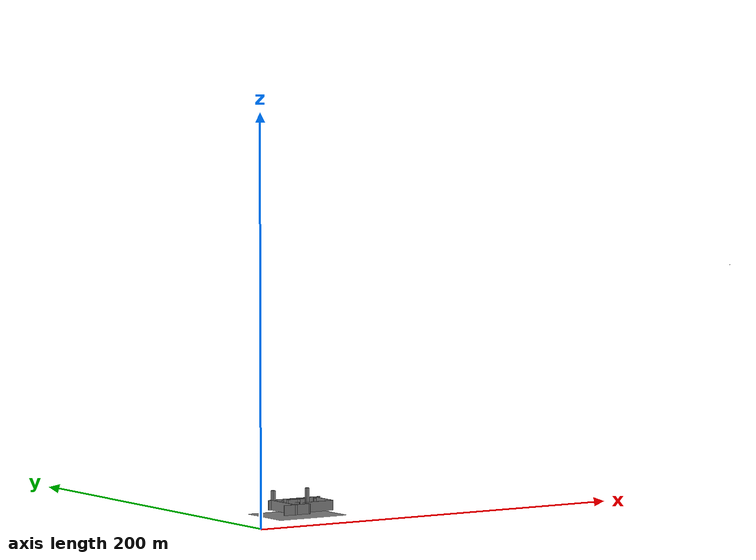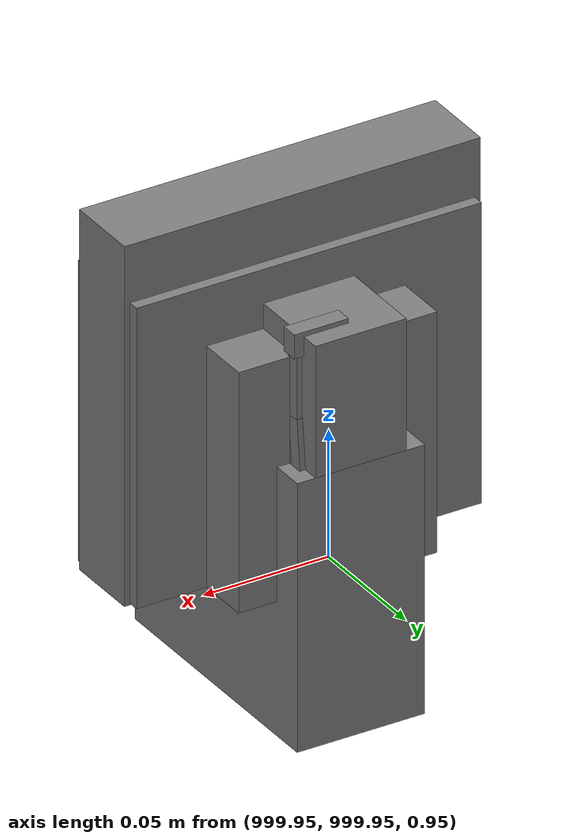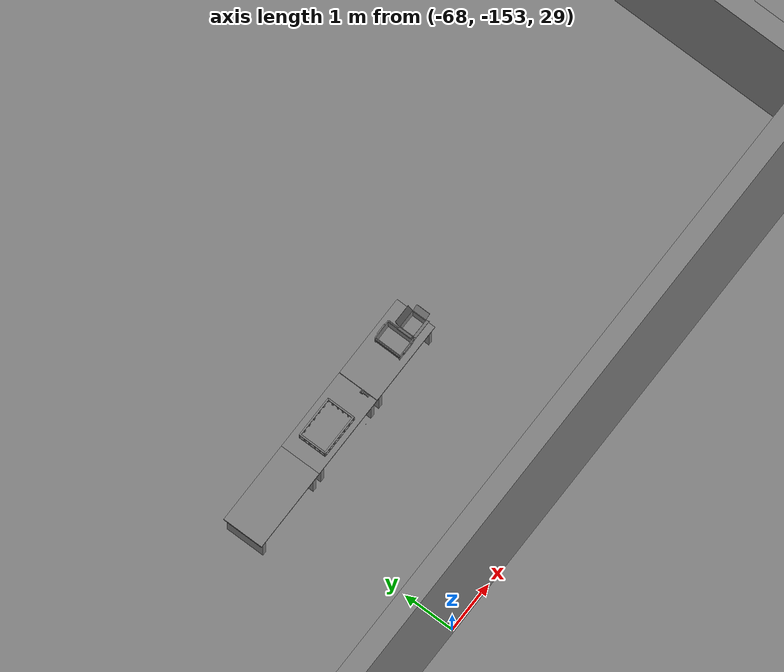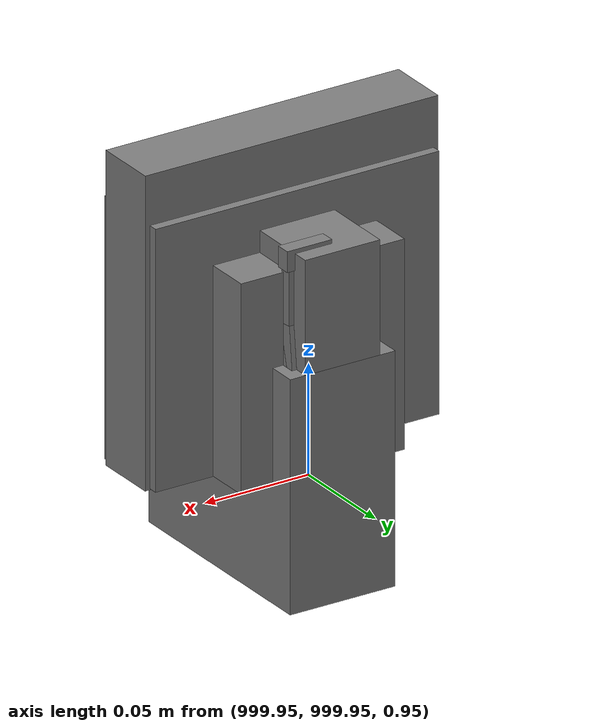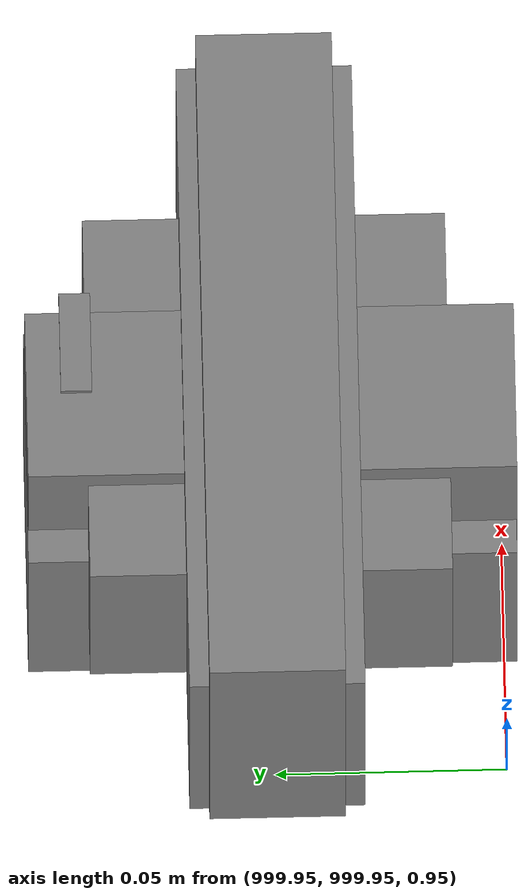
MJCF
<mujoco>
    <option gravity="0.000000000 0.000000000 -9.810000420" timestep="0.0049999999" integrator="implicitfast" density="1.225" viscosity="1.8000001e-05" noslip_iterations="10" iterations="100" sdf_iterations="50">
        <flag multiccd="disable"/>
    </option>
    <size memory="1000M"/>
    <compiler coordinate="local"/>
    <worldbody>
        <light cutoff="30" pos="0 1 1" dir="0 -1 -2"/>
        <light cutoff="30" pos="0 -1 1" dir="0 1 -2"/>
        <body pos="-65.899940491 -149.568130493 31.167160034" euler="-46.425231934 49.860488892 -73.580718994" mocap="true" name="spotlight6_SpotLight"/>
        <body pos="1000.000000000 1000.000000000 1.000000000" euler="0.000000000 0.000000000 180.000000000" name="openloong_gripper_2f85_fix_base_usda_wifi_box">
            <geom contype="1" conaffinity="1" density="1000" type="box" material="" rgba="0.500000000 0.500000000 0.500000000 1.000000000" solimp="0.899999976 0.949999988 0.001000000" friction="1.000000000 0.005000000 0.000100000" solref="0.020000000 1.000000000" margin="0" condim="3" group="0" pos="0.000000000 0.000000000 0.058978677" quat="0.000000000 0.000000047 0.000000000 1.000000000" size="0.068499997 0.018999999 0.059000000" name="openloong_gripper_2f85_fix_base_usda_geom_63255C83_4529_48F1_B52A_F161FB1FF921"/>
            <freejoint name="openloong_gripper_2f85_fix_base_usda_wifi_box_joint"/>
            <site size="0.005000000 0.005000000 0.005000000" rgba="0.500000000 0.500000000 0.500000000 1.000000000" pos="0.000000000 0.000000000 0.000000000" quat="0.999961913 0.008726500 0.000000000 0.000000000" group="0" type="sphere" name="openloong_gripper_2f85_fix_base_usda_wifi_boxsite"/>
        </body>
        <body pos="1000.000000000 1000.000000000 1.000000000" euler="0.000000000 0.000000000 180.000000000" name="openloong_gripper_2f85_fix_base_usda_cpu_fan">
            <geom contype="1" conaffinity="1" density="1000" type="box" material="" rgba="0.500000000 0.500000000 0.500000000 1.000000000" solimp="0.899999976 0.949999988 0.001000000" friction="1.000000000 0.005000000 0.000100000" solref="0.020000000 1.000000000" margin="0" condim="3" group="0" pos="0.000000000 0.000000000 0.070034981" quat="0.000000000 0.000000000 0.000000000 1.000000000" size="0.070700005 0.014699999 0.070700005" name="openloong_gripper_2f85_fix_base_usda_geom_D1CE93AB_4262_4AE5_BDF5_73F68A386309"/>
            <freejoint name="openloong_gripper_2f85_fix_base_usda_cpu_fan_joint"/>
            <site size="0.005000000 0.005000000 0.005000000" rgba="0.500000000 0.500000000 0.500000000 1.000000000" pos="0.000000000 0.000000000 0.000000000" quat="0.999961913 0.008726535 0.000000000 0.000000000" group="0" type="sphere" name="openloong_gripper_2f85_fix_base_usda_cpu_fancsite"/>
        </body>
        <body pos="1000.000000000 999.999938965 1.000000000" euler="0.000000000 0.000000000 180.000000000" name="openloong_gripper_2f85_fix_base_usda_intelcore_i5">
            <geom contype="1" conaffinity="1" density="1000" type="box" material="" rgba="0.500000000 0.500000000 0.500000000 1.000000000" solimp="0.899999976 0.949999988 0.001000000" friction="1.000000000 0.005000000 0.000100000" solref="0.020000000 1.000000000" margin="0" condim="3" group="0" pos="0.000000000 0.000000000 0.051722717" quat="0.707106709 0.000000000 0.000000000 -0.707106769" size="0.052800000 0.018080002 0.052800000" name="openloong_gripper_2f85_fix_base_usda_geom_FCF8DFAD_E1A6_446A_85A6_FB195962527C"/>
            <freejoint name="openloong_gripper_2f85_fix_base_usda_intelcore_i5_joint"/>
            <site size="0.005000000 0.005000000 0.005000000" rgba="0.500000000 0.500000000 0.500000000 1.000000000" pos="0.000000000 0.000000000 0.000000000" quat="0.999961913 0.008726534 0.000000000 0.000000000" group="0" type="sphere" name="openloong_gripper_2f85_fix_base_usda_intelcore_i5site"/>
        </body>
        <body pos="-66.076530457 -149.157394409 31.162017822" euler="123.792594910 60.306503296 72.687515259" mocap="true" name="spotlight2_SpotLight"/>
        <body pos="-66.365653992 -149.485534668 31.170408249" euler="-2.388014317 -72.789474487 -49.224182129" mocap="true" name="spotlight5_SpotLight"/>
        <body pos="1000.000000000 1000.000000000 1.000000000" euler="0.000011953 0.000005123 -179.999984741" name="openloong_gripper_2f85_fix_base_usda_intel_box">
            <geom contype="1" conaffinity="1" density="1000" type="box" material="" rgba="0.500000000 0.500000000 0.500000000 1.000000000" solimp="0.899999976 0.949999988 0.001000000" friction="1.000000000 0.005000000 0.000100000" solref="0.020000000 1.000000000" margin="0" condim="3" group="0" pos="0.000000000 -0.000067139 0.000082284" quat="0.707106709 0.000000225 0.000000253 0.707106650" size="0.052800003 0.025300000 0.052800003" name="openloong_gripper_2f85_fix_base_usda_geom_8D0DE8BC_A8CD_4C81_874A_91F0B28B2DF5"/>
            <freejoint name="openloong_gripper_2f85_fix_base_usda_intel_box_joint"/>
            <site size="0.005000000 0.005000000 0.005000000" rgba="0.500000000 0.500000000 0.500000000 1.000000000" pos="0.000000000 0.000000000 0.000000000" quat="0.999961913 0.008726500 0.000000000 0.000000000" group="0" type="sphere" name="openloong_gripper_2f85_fix_base_usda_intel_boxsite"/>
        </body>
        <body pos="1000.000000000 1000.000000000 1.000000000" euler="0.000000000 0.000000000 180.000000000" name="openloong_gripper_2f85_fix_base_usda_battery_01">
            <geom contype="1" conaffinity="1" density="1000" type="box" material="" rgba="0.500000000 0.500000000 0.500000000 1.000000000" solimp="0.899999976 0.949999988 0.001000000" friction="1.000000000 0.005000000 0.000100000" solref="0.020000000 1.000000000" margin="0" condim="3" group="0" pos="-0.011123657 -0.041940309 0.101691343" quat="1.000000000 0.000000000 0.000000000 0.000000000" size="0.010800000 0.003375000 0.004725000" name="openloong_gripper_2f85_fix_base_usda_geom_956CBE50_6BFC_40B2_9D7B_25AD6F1FD3EF"/>
            <geom contype="1" conaffinity="1" density="1000" type="box" material="" rgba="0.500000000 0.500000000 0.500000000 1.000000000" solimp="0.899999976 0.949999988 0.001000000" friction="1.000000000 0.005000000 0.000100000" solref="0.020000000 1.000000000" margin="0" condim="3" group="0" pos="-0.010876465 -0.044247437 0.047066893" quat="0.998702705 -0.050920475 0.000000000 0.000000000" size="0.009450001 0.002700000 0.024975000" name="openloong_gripper_2f85_fix_base_usda_geom_3FE8C7B3_A1D2_4F68_A1DE_402E1385D14D"/>
            <geom contype="1" conaffinity="1" density="1000" type="box" material="" rgba="0.500000000 0.500000000 0.500000000 1.000000000" solimp="0.899999976 0.949999988 0.001000000" friction="1.000000000 0.005000000 0.000100000" solref="0.020000000 1.000000000" margin="0" condim="3" group="0" pos="-0.001235962 -0.000659180 0.047381196" quat="1.000000000 0.000000000 0.000000000 0.000000000" size="0.039420001 0.039150000 0.047250003" name="openloong_gripper_2f85_fix_base_usda_geom_7C2498AE_1418_4691_8682_279CAC7F12FE"/>
            <geom contype="1" conaffinity="1" density="1000" type="box" material="" rgba="0.500000000 0.500000000 0.500000000 1.000000000" solimp="0.899999976 0.949999988 0.001000000" friction="1.000000000 0.005000000 0.000100000" solref="0.020000000 1.000000000" margin="0" condim="3" group="0" pos="-0.010876465 -0.039138794 0.009851727" quat="1.000000000 0.000000000 0.000000000 0.000000000" size="0.009450001 0.010800000 0.013500000" name="openloong_gripper_2f85_fix_base_usda_geom_417689E8_9606_40E0_9AC6_D757F1AB54C3"/>
            <geom contype="1" conaffinity="1" density="1000" type="box" material="" rgba="0.500000000 0.500000000 0.500000000 1.000000000" solimp="0.899999976 0.949999988 0.001000000" friction="1.000000000 0.005000000 0.000100000" solref="0.020000000 1.000000000" margin="0" condim="3" group="0" pos="-0.010876465 -0.041528322 0.071508206" quat="1.000000000 0.000000000 0.000000000 0.000000000" size="0.009450001 0.002700000 0.027000001" name="openloong_gripper_2f85_fix_base_usda_geom_7707DCEF_CD24_4401_BE3C_2A1DD143BD0A"/>
            <freejoint name="openloong_gripper_2f85_fix_base_usda_battery_01_joint"/>
            <site size="0.005000000 0.005000000 0.005000000" rgba="0.500000000 0.500000000 0.500000000 1.000000000" pos="0.000000000 0.000000000 0.000000000" quat="0.999961913 0.008726500 0.000000000 0.000000000" group="0" type="sphere" name="openloong_gripper_2f85_fix_base_usda_battery_01site"/>
        </body>
        <body pos="-64.866622925 -149.383972168 30.183746338" euler="89.999984741 89.999946594 0.000000000" name="openloong_gripper_2f85_fix_base_usda_bluebox_01">
            <geom contype="1" conaffinity="1" density="1000" type="box" material="" rgba="0.500000000 0.500000000 0.500000000 1.000000000" solimp="0.899999976 0.949999988 0.001000000" friction="1.000000000 0.005000000 0.000100000" solref="0.020000000 1.000000000" margin="0" condim="3" group="0" pos="0.276580811 0.187225342 0.000068665" quat="0.707106948 0.000077471 0.707106352 0.000077486" size="0.100000001 0.057999998 0.010000000" name="openloong_gripper_2f85_fix_base_usda_geom_2E8930F1_0501_40F2_AEBB_8A657A7C43ED"/>
            <geom contype="1" conaffinity="1" density="1000" type="box" material="" rgba="0.500000000 0.500000000 0.500000000 1.000000000" solimp="0.899999976 0.949999988 0.001000000" friction="1.000000000 0.005000000 0.000100000" solref="0.020000000 1.000000000" margin="0" condim="3" group="0" pos="0.000000000 0.002883911 0.000000000" quat="0.999999881 0.000000000 0.000000000 0.000000000" size="0.254000008 0.003000000 0.172000006" name="openloong_gripper_2f85_fix_base_usda_geom_B30DE01E_F9B4_40ED_AF8C_4D25C798D4B3"/>
            <geom contype="1" conaffinity="1" density="1000" type="box" material="" rgba="0.500000000 0.500000000 0.500000000 1.000000000" solimp="0.899999976 0.949999988 0.001000000" friction="1.000000000 0.005000000 0.000100000" solref="0.020000000 1.000000000" margin="0" condim="3" group="0" pos="0.000000000 0.124874115 0.173484802" quat="0.999796331 0.020176515 -0.000000015 0.000000030" size="0.259999990 0.119999997 0.007000000" name="openloong_gripper_2f85_fix_base_usda_geom_98B3A761_58B5_43F1_BCC3_D21B28157A6A"/>
            <geom contype="1" conaffinity="1" density="1000" type="box" material="" rgba="0.500000000 0.500000000 0.500000000 1.000000000" solimp="0.899999976 0.949999988 0.001000000" friction="1.000000000 0.005000000 0.000100000" solref="0.020000000 1.000000000" margin="0" condim="3" group="0" pos="0.000000000 0.124874115 -0.173469543" quat="0.999796331 -0.020176545 -0.000000015 0.000000000" size="0.259999990 0.119999997 0.007000000" name="openloong_gripper_2f85_fix_base_usda_geom_32793E9E_6C4D_41BB_A167_456E316A554F"/>
            <geom contype="1" conaffinity="1" density="1000" type="box" material="" rgba="0.500000000 0.500000000 0.500000000 1.000000000" solimp="0.899999976 0.949999988 0.001000000" friction="1.000000000 0.005000000 0.000100000" solref="0.020000000 1.000000000" margin="0" condim="3" group="0" pos="0.000000000 0.214008331 0.188980103" quat="0.999912977 0.013176724 0.000000015 0.000000000" size="0.259999990 0.029999999 0.012500000" name="openloong_gripper_2f85_fix_base_usda_geom_491F2E6A_C948_4B36_88C2_6C2065F34BF1"/>
            <geom contype="1" conaffinity="1" density="1000" type="box" material="" rgba="0.500000000 0.500000000 0.500000000 1.000000000" solimp="0.899999976 0.949999988 0.001000000" friction="1.000000000 0.005000000 0.000100000" solref="0.020000000 1.000000000" margin="0" condim="3" group="0" pos="-0.258361816 0.125289917 0.001876831" quat="0.702796936 -0.020792112 0.710783124 0.020769298" size="0.189999998 0.119999997 0.009000000" name="openloong_gripper_2f85_fix_base_usda_geom_921A65F9_9AA4_497E_A357_9C33B065DBA8"/>
            <geom contype="1" conaffinity="1" density="1000" type="box" material="" rgba="0.500000000 0.500000000 0.500000000 1.000000000" solimp="0.899999976 0.949999988 0.001000000" friction="1.000000000 0.005000000 0.000100000" solref="0.020000000 1.000000000" margin="0" condim="3" group="0" pos="0.000000000 0.214008331 -0.188980103" quat="0.999912977 -0.013176769 0.000000030 0.000000015" size="0.259999990 0.029999999 0.012500000" name="openloong_gripper_2f85_fix_base_usda_geom_235B44B3_C977_4D2C_9B5A_EA8ED523DB63"/>
            <geom contype="1" conaffinity="1" density="1000" type="box" material="" rgba="0.500000000 0.500000000 0.500000000 1.000000000" solimp="0.899999976 0.949999988 0.001000000" friction="1.000000000 0.005000000 0.000100000" solref="0.020000000 1.000000000" margin="0" condim="3" group="0" pos="-0.276611328 0.187225342 0.000068665" quat="0.707106650 0.000077441 0.707106709 0.000077456" size="0.100000001 0.057999998 0.010000000" name="openloong_gripper_2f85_fix_base_usda_geom_2792555A_0D88_4F70_B9E0_563767486B6D"/>
            <geom contype="1" conaffinity="1" density="1000" type="box" material="" rgba="0.500000000 0.500000000 0.500000000 1.000000000" solimp="0.899999976 0.949999988 0.001000000" friction="1.000000000 0.005000000 0.000100000" solref="0.020000000 1.000000000" margin="0" condim="3" group="0" pos="0.258331299 0.125289917 0.001876831" quat="0.702851415 0.018856421 0.710823774 -0.019329369" size="0.189999998 0.119999997 0.009000000" name="openloong_gripper_2f85_fix_base_usda_geom_9003D8CF_4850_4F94_B04B_8FE206C73213"/>
            <freejoint name="openloong_gripper_2f85_fix_base_usda_bluebox_01_joint"/>
            <site size="0.005000000 0.005000000 0.005000000" rgba="0.500000000 0.500000000 0.500000000 1.000000000" pos="0.000000000 0.000000000 0.000000000" quat="0.999961913 0.008726534 0.000000000 0.000000000" group="0" type="sphere" name="openloong_gripper_2f85_fix_base_usda_bluebox_01site"/>
        </body>
        <body pos="-64.496299744 -149.491867065 30.235729218" euler="0.000000000 0.000000000 89.999946594" name="openloong_gripper_2f85_fix_base_usda_cardboardbox_01">
            <geom contype="1" conaffinity="1" density="1000" type="box" material="" rgba="0.500000000 0.500000000 0.500000000 1.000000000" solimp="0.899999976 0.949999988 0.001000000" friction="1.000000000 0.005000000 0.000100000" solref="0.020000000 1.000000000" margin="0" condim="3" group="0" pos="-0.003166199 -0.004086494 0.005052090" quat="1.000000000 0.000000000 0.000000000 0.000000000" size="0.142499998 0.177500010 0.005000000" name="openloong_gripper_2f85_fix_base_usda_geom_63587A3F_C7EB_471F_A8DE_3EDB6E23F26F"/>
            <geom contype="1" conaffinity="1" density="1000" type="box" material="" rgba="0.500000000 0.500000000 0.500000000 1.000000000" solimp="0.899999976 0.949999988 0.001000000" friction="1.000000000 0.005000000 0.000100000" solref="0.020000000 1.000000000" margin="0" condim="3" group="0" pos="-0.003166199 0.170316696 0.150570869" quat="1.000000000 0.000000000 0.000000000 0.000000000" size="0.142499998 0.005000000 0.149999991" name="openloong_gripper_2f85_fix_base_usda_geom_A10664E9_FF97_4419_A7AA_27D77DD92938"/>
            <geom contype="1" conaffinity="1" density="1000" type="box" material="" rgba="0.500000000 0.500000000 0.500000000 1.000000000" solimp="0.899999976 0.949999988 0.001000000" friction="1.000000000 0.005000000 0.000100000" solref="0.020000000 1.000000000" margin="0" condim="3" group="0" pos="-0.147399902 -0.005307198 0.150570869" quat="1.000000000 0.000000000 0.000000000 0.000000000" size="0.005000000 0.177500010 0.149999991" name="openloong_gripper_2f85_fix_base_usda_geom_17615BBC_BB06_4D28_B521_DF63888833A7"/>
            <geom contype="1" conaffinity="1" density="1000" type="box" material="" rgba="0.500000000 0.500000000 0.500000000 1.000000000" solimp="0.899999976 0.949999988 0.001000000" friction="1.000000000 0.005000000 0.000100000" solref="0.020000000 1.000000000" margin="0" condim="3" group="0" pos="0.140275955 -0.005307198 0.150570869" quat="1.000000000 0.000000000 0.000000000 0.000000000" size="0.005000000 0.177500010 0.149999991" name="openloong_gripper_2f85_fix_base_usda_geom_7DEF08C5_1363_4166_AC0B_EF4299F91CED"/>
            <geom contype="1" conaffinity="1" density="1000" type="box" material="" rgba="0.500000000 0.500000000 0.500000000 1.000000000" solimp="0.899999976 0.949999988 0.001000000" friction="1.000000000 0.005000000 0.000100000" solref="0.020000000 1.000000000" margin="0" condim="3" group="0" pos="-0.003166199 -0.181550980 0.150570869" quat="1.000000000 0.000000000 0.000000000 0.000000000" size="0.142499998 0.005000000 0.149999991" name="openloong_gripper_2f85_fix_base_usda_geom_938749E2_9FB6_4F5A_A872_27C72A1F8ABA"/>
            <freejoint name="openloong_gripper_2f85_fix_base_usda_cardboardbox_01_joint"/>
            <site size="0.005000000 0.005000000 0.005000000" rgba="0.500000000 0.500000000 0.500000000 1.000000000" pos="0.000000000 0.000000000 0.000000000" quat="0.999961913 0.008726535 0.000000000 0.000000000" group="0" type="sphere" name="openloong_gripper_2f85_fix_base_usda_site_EE40B997_07FF_4F6F_97B0_3A3300134215"/>
            <body pos="0.139160156 -0.004048347 0.301930904" euler="-179.999954224 49.383502960 179.999954224" name="openloong_gripper_2f85_fix_base_usda_A1_006">
                <geom contype="1" conaffinity="1" density="1000" type="box" material="" rgba="0.500000000 0.500000000 0.500000000 1.000000000" solimp="0.899999976 0.949999988 0.001000000" friction="1.000000000 0.005000000 0.000100000" solref="0.020000000 1.000000000" margin="0" condim="3" group="0" pos="-0.071587563 0.000009537 0.001745224" quat="0.999999881 0.000000000 0.000000000 0.000000000" size="0.071249999 0.179999992 0.002500000" name="openloong_gripper_2f85_fix_base_usda_geom_13412EB8_43E6_4724_B455_96C46D79CF16"/>
                <joint armature="0" stiffness="0.07" damping="0.0099999998" axis="0.000000 1.000000 0.000000" type="hinge" name="openloong_gripper_2f85_fix_base_usda_A1_006"/>
            </body>
            <body pos="-0.145902634 -0.004086494 0.301938057" euler="-180.000000000 -60.000011444 -180.000000000" name="openloong_gripper_2f85_fix_base_usda_A2_006">
                <geom contype="1" conaffinity="1" density="1000" type="box" material="" rgba="0.500000000 0.500000000 0.500000000 1.000000000" solimp="0.899999976 0.949999988 0.001000000" friction="1.000000000 0.005000000 0.000100000" solref="0.020000000 1.000000000" margin="0" condim="3" group="0" pos="0.071268082 0.000009537 0.002717972" quat="0.000002921 0.000000000 -0.000000030 0.999999881" size="0.071249999 0.179999992 0.002500000" name="openloong_gripper_2f85_fix_base_usda_geom_3CF4B64F_66A7_43E2_AF7D_9A2BB90D5014"/>
                <joint armature="0" stiffness="0.07" damping="0.0099999998" axis="0.000000 1.000000 0.000000" type="hinge" name="openloong_gripper_2f85_fix_base_usda_A2_006"/>
            </body>
            <body pos="-0.003385544 0.175991058 0.301930904" euler="-125.858116150 -0.000004561 0.000002331" name="openloong_gripper_2f85_fix_base_usda_B2_006">
                <geom contype="1" conaffinity="1" density="1000" type="box" material="" rgba="0.500000000 0.500000000 0.500000000 1.000000000" solimp="0.899999976 0.949999988 0.001000000" friction="1.000000000 0.005000000 0.000100000" solref="0.020000000 1.000000000" margin="0" condim="3" group="0" pos="0.000009537 -0.070939064 -0.002470016" quat="0.999614120 0.027776197 -0.000000015 0.000000030" size="0.137500003 0.064999998 0.005000000" name="openloong_gripper_2f85_fix_base_usda_geom_AE118E7B_358F_4250_991E_EAAF534AC709"/>
                <joint armature="0" stiffness="0.07" damping="0.0099999998" axis="1.000000 0.000000 0.000000" type="hinge" name="openloong_gripper_2f85_fix_base_usda_B2_006"/>
            </body>
            <body pos="-0.003385544 -0.184140205 0.301938057" euler="147.805557251 0.000000000 0.000000000" name="openloong_gripper_2f85_fix_base_usda_B1_006">
                <geom contype="1" conaffinity="1" density="1000" type="box" material="" rgba="0.500000000 0.500000000 0.500000000 1.000000000" solimp="0.899999976 0.949999988 0.001000000" friction="1.000000000 0.005000000 0.000100000" solref="0.020000000 1.000000000" margin="0" condim="3" group="0" pos="-0.000028610 0.070202351 -0.002703667" quat="0.999614179 -0.027776167 0.000000000 0.000000000" size="0.137500003 0.064999998 0.005000000" name="openloong_gripper_2f85_fix_base_usda_geom_032270BE_71ED_4ADD_9D3C_3430F97E2575"/>
                <joint armature="0" stiffness="0.07" damping="0.0099999998" axis="1.000000 0.000000 0.000000" type="hinge" name="openloong_gripper_2f85_fix_base_usda_B1_006"/>
            </body>
        </body>
        <body pos="-65.882858276 -149.481979370 30.229999542" euler="-64.487716675 0.000000000 0.000000000" name="openloong_gripper_2f85_fix_base_usda_Barcode">
            <geom contype="1" conaffinity="1" density="1000" type="box" material="" rgba="0.500000000 0.500000000 0.500000000 1.000000000" solimp="0.899999976 0.949999988 0.001000000" friction="1.000000000 0.005000000 0.000100000" solref="0.020000000 1.000000000" margin="0" condim="3" group="0" pos="0.000000000 0.013038635 0.001419067" quat="0.000000000 0.000000000 0.000000000 1.000000119" size="0.034000002 0.010000000 0.017999999" name="openloong_gripper_2f85_fix_base_usda_geom_E2C238C5_D764_41F5_899D_02F7FC1D12F6"/>
            <geom contype="1" conaffinity="1" density="1000" type="box" material="" rgba="0.500000000 0.500000000 0.500000000 1.000000000" solimp="0.899999976 0.949999988 0.001000000" friction="1.000000000 0.005000000 0.000100000" solref="0.020000000 1.000000000" margin="0" condim="3" group="0" pos="0.000000000 -0.035301208 -0.007095337" quat="0.000000000 0.000000000 -0.043619365 0.999048233" size="0.028999999 0.010000000 0.020000000" name="openloong_gripper_2f85_fix_base_usda_geom_05E33ADF_AEC9_429E_A1B3_15267D8B7070"/>
            <geom contype="1" conaffinity="1" density="1000" type="box" material="" rgba="0.500000000 0.500000000 0.500000000 1.000000000" solimp="0.899999976 0.949999988 0.001000000" friction="1.000000000 0.005000000 0.000100000" solref="0.020000000 1.000000000" margin="0" condim="3" group="0" pos="0.000000000 -0.043411255 -0.011749268" quat="0.922262907 0.386563420 0.000000000 0.000000000" size="0.026000001 0.010000000 0.020000000" name="openloong_gripper_2f85_fix_base_usda_geom_A93D4164_7B4F_49CC_A593_92C0B1F046AE"/>
            <geom contype="1" conaffinity="1" density="1000" type="box" material="" rgba="0.500000000 0.500000000 0.500000000 1.000000000" solimp="0.899999976 0.949999988 0.001000000" friction="1.000000000 0.005000000 0.000100000" solref="0.020000000 1.000000000" margin="0" condim="3" group="0" pos="0.000000000 -0.016967773 -0.031860352" quat="0.000000000 0.000000000 0.000000000 1.000000119" size="0.008000000 0.010000000 0.013000000" name="openloong_gripper_2f85_fix_base_usda_geom_B8B0A2AE_0E38_49DA_9A0D_8B3FA0578878"/>
            <geom contype="1" conaffinity="1" density="1000" type="box" material="" rgba="0.500000000 0.500000000 0.500000000 1.000000000" solimp="0.899999976 0.949999988 0.001000000" friction="1.000000000 0.005000000 0.000100000" solref="0.020000000 1.000000000" margin="0" condim="3" group="0" pos="0.000000000 -0.001869202 0.000312805" quat="0.953716993 0.300705761 0.000000000 0.000000000" size="0.032000002 0.010000000 0.018999999" name="openloong_gripper_2f85_fix_base_usda_geom_AA61CB45_ED0B_41B3_A3CB_8AD0D785E069"/>
            <geom contype="1" conaffinity="1" density="1000" type="box" material="" rgba="0.500000000 0.500000000 0.500000000 1.000000000" solimp="0.899999976 0.949999988 0.001000000" friction="1.000000000 0.005000000 0.000100000" solref="0.020000000 1.000000000" margin="0" condim="3" group="0" pos="0.000000000 -0.019531250 -0.003173828" quat="0.953716993 0.300705761 0.000000000 0.000000000" size="0.030999999 0.010000000 0.020000000" name="openloong_gripper_2f85_fix_base_usda_geom_CD8B13FC_0C39_4F8B_AE28_78DF63E3CD71"/>
            <geom contype="1" conaffinity="1" density="1000" type="box" material="" rgba="0.500000000 0.500000000 0.500000000 1.000000000" solimp="0.899999976 0.949999988 0.001000000" friction="1.000000000 0.005000000 0.000100000" solref="0.020000000 1.000000000" margin="0" condim="3" group="0" pos="0.000000000 -0.035301208 -0.007095337" quat="0.953716993 0.300705761 0.000000000 0.000000000" size="0.028999999 0.010000000 0.020000000" name="openloong_gripper_2f85_fix_base_usda_geom_476C8FB9_C01A_40D8_B7D1_2553835A5EF3"/>
            <geom contype="1" conaffinity="1" density="1000" type="box" material="" rgba="0.500000000 0.500000000 0.500000000 1.000000000" solimp="0.899999976 0.949999988 0.001000000" friction="1.000000000 0.005000000 0.000100000" solref="0.020000000 1.000000000" margin="0" condim="3" group="0" pos="0.000000000 -0.042617798 -0.071121216" quat="0.000000000 0.000000000 0.000000000 1.000000119" size="0.013000000 0.021000000 0.059999999" name="openloong_gripper_2f85_fix_base_usda_geom_1D6CA421_CBED_48E7_999B_1F9B0D0D9517"/>
            <freejoint name="openloong_gripper_2f85_fix_base_usda_Barcode_joint"/>
            <site size="0.005000000 0.005000000 0.005000000" rgba="0.500000000 0.500000000 0.500000000 1.000000000" pos="0.000000000 0.000000000 0.000000000" quat="1.000000000 0.000000000 0.000000000 0.000000000" group="0" type="sphere" name="openloong_gripper_2f85_fix_base_usda_Barcode_site"/>
        </body>
        <body pos="-66.745018005 -149.392349243 30.184000015" euler="0.000000000 0.000000000 89.999946594" name="[22332354780228]_Basket_01">
            <geom contype="1" conaffinity="1" density="1000" type="box" material="" rgba="0.500000000 0.500000000 0.500000000 1.000000000" solimp="0.899999976 0.949999988 0.001000000" friction="1.000000000 0.005000000 0.000100000" solref="0.020000000 1.000000000" margin="0" condim="3" group="0" pos="-0.052425385 0.389207840 0.089787483" quat="0.707107008 0.000000000 0.000000000 0.707106411" size="0.014249999 0.014249999 0.059999999" name="[22332354780228]_geom_4DED6509_69AA_4E70_B561_3CFD52B272B6"/>
            <geom contype="1" conaffinity="1" density="1000" type="box" material="" rgba="0.500000000 0.500000000 0.500000000 1.000000000" solimp="0.899999976 0.949999988 0.001000000" friction="1.000000000 0.005000000 0.000100000" solref="0.020000000 1.000000000" margin="0" condim="3" group="0" pos="0.264015198 -0.133043289 0.089787483" quat="0.707107008 0.000000000 0.000000000 0.707106411" size="0.014249999 0.014249999 0.059999999" name="[22332354780228]_geom_8A6900D8_8655_465F_BB8A_155A0162EAD6"/>
            <geom contype="1" conaffinity="1" density="1000" type="box" material="" rgba="0.500000000 0.500000000 0.500000000 1.000000000" solimp="0.899999976 0.949999988 0.001000000" friction="1.000000000 0.005000000 0.000100000" solref="0.020000000 1.000000000" margin="0" condim="3" group="0" pos="-0.264015198 -0.265548706 0.089793205" quat="0.707107008 0.000000000 0.000000000 0.707106411" size="0.014249999 0.014249999 0.059999999" name="[22332354780228]_geom_FE8B632F_7122_42CC_BA0E_CB5FBE847BFA"/>
            <geom contype="1" conaffinity="1" density="1000" type="box" material="" rgba="0.500000000 0.500000000 0.500000000 1.000000000" solimp="0.899999976 0.949999988 0.001000000" friction="1.000000000 0.005000000 0.000100000" solref="0.020000000 1.000000000" margin="0" condim="3" group="0" pos="-0.160263062 -0.389322281 0.089793205" quat="0.707107008 0.000000000 0.000000000 0.707106411" size="0.014249999 0.014249999 0.059999999" name="[22332354780228]_geom_317A2C02_EE43_4D0E_A1D1_E5CA6CCDE52A"/>
            <geom contype="1" conaffinity="1" density="1000" type="box" material="" rgba="0.500000000 0.500000000 0.500000000 1.000000000" solimp="0.899999976 0.949999988 0.001000000" friction="1.000000000 0.005000000 0.000100000" solref="0.020000000 1.000000000" margin="0" condim="3" group="0" pos="0.162265778 -0.389322281 0.089787483" quat="0.707107008 0.000000000 0.000000000 0.707106411" size="0.014249999 0.014249999 0.059999999" name="[22332354780228]_geom_025D21DD_A5ED_46F2_9E66_40577170259D"/>
            <geom contype="1" conaffinity="1" density="1000" type="box" material="" rgba="0.500000000 0.500000000 0.500000000 1.000000000" solimp="0.899999976 0.949999988 0.001000000" friction="1.000000000 0.005000000 0.000100000" solref="0.020000000 1.000000000" margin="0" condim="3" group="0" pos="0.264015198 0.389207840 0.089787483" quat="0.707107008 0.000000000 0.000000000 0.707106411" size="0.014249999 0.014249999 0.059999999" name="[22332354780228]_geom_92C81949_25BB_49BC_9B2B_C5825F1DA1EC"/>
            <geom contype="1" conaffinity="1" density="1000" type="box" material="" rgba="0.500000000 0.500000000 0.500000000 1.000000000" solimp="0.899999976 0.949999988 0.001000000" friction="1.000000000 0.005000000 0.000100000" solref="0.020000000 1.000000000" margin="0" condim="3" group="0" pos="-0.264015198 -0.133043289 0.089793205" quat="0.707107008 0.000000000 0.000000000 0.707106411" size="0.014249999 0.014249999 0.059999999" name="[22332354780228]_geom_CAB01008_0D00_40C4_B9A6_97BE0C239835"/>
            <geom contype="1" conaffinity="1" density="1000" type="box" material="" rgba="0.500000000 0.500000000 0.500000000 1.000000000" solimp="0.899999976 0.949999988 0.001000000" friction="1.000000000 0.005000000 0.000100000" solref="0.020000000 1.000000000" margin="0" condim="3" group="0" pos="-0.264026642 0.269256592 0.089793205" quat="0.707107008 0.000000000 0.000000000 0.707106411" size="0.014249999 0.014249999 0.059999999" name="[22332354780228]_geom_AD4CE3DE_2F51_4043_BBFD_B6E73442327A"/>
            <geom contype="1" conaffinity="1" density="1000" type="box" material="" rgba="0.500000000 0.500000000 0.500000000 1.000000000" solimp="0.899999976 0.949999988 0.001000000" friction="1.000000000 0.005000000 0.000100000" solref="0.020000000 1.000000000" margin="0" condim="3" group="0" pos="0.054462433 0.389207840 0.089787483" quat="0.707107008 0.000000000 0.000000000 0.707106411" size="0.014249999 0.014249999 0.059999999" name="[22332354780228]_geom_0953AA47_84DA_4C0B_9DC6_88486C49E8DB"/>
            <geom contype="1" conaffinity="1" density="1000" type="box" material="" rgba="0.500000000 0.500000000 0.500000000 1.000000000" solimp="0.899999976 0.949999988 0.001000000" friction="1.000000000 0.005000000 0.000100000" solref="0.020000000 1.000000000" margin="0" condim="3" group="0" pos="0.054462433 -0.389322281 0.089787483" quat="0.707107008 0.000000000 0.000000000 0.707106411" size="0.014249999 0.014249999 0.059999999" name="[22332354780228]_geom_D4CEEF39_99EA_4A73_A2A3_6E2CD08B6261"/>
            <geom contype="1" conaffinity="1" density="1000" type="box" material="" rgba="0.500000000 0.500000000 0.500000000 1.000000000" solimp="0.899999976 0.949999988 0.001000000" friction="1.000000000 0.005000000 0.000100000" solref="0.020000000 1.000000000" margin="0" condim="3" group="0" pos="0.264015198 0.269256592 0.089793205" quat="0.707107008 0.000000000 0.000000000 0.707106411" size="0.014249999 0.014249999 0.059999999" name="[22332354780228]_geom_5087F20F_97F7_4812_A6F9_D223FCC8B616"/>
            <geom contype="1" conaffinity="1" density="1000" type="box" material="" rgba="0.500000000 0.500000000 0.500000000 1.000000000" solimp="0.899999976 0.949999988 0.001000000" friction="1.000000000 0.005000000 0.000100000" solref="0.020000000 1.000000000" margin="0" condim="3" group="0" pos="0.264015198 -0.389322281 0.089787483" quat="0.707107008 0.000000000 0.000000000 0.707106411" size="0.014249999 0.014249999 0.059999999" name="[22332354780228]_geom_4CAA3791_8873_44AC_8291_DC96453AD95F"/>
            <geom contype="1" conaffinity="1" density="1000" type="box" material="" rgba="0.500000000 0.500000000 0.500000000 1.000000000" solimp="0.899999976 0.949999988 0.001000000" friction="1.000000000 0.005000000 0.000100000" solref="0.020000000 1.000000000" margin="0" condim="3" group="0" pos="0.000000000 0.000000000 0.015998840" quat="0.707107008 0.000000000 0.000000000 0.707106411" size="0.403499991 0.279000014 0.015750000" name="[22332354780228]_geom_36F16277_9BEE_401B_B7DB_2F93379B5C86"/>
            <geom contype="1" conaffinity="1" density="1000" type="box" material="" rgba="0.500000000 0.500000000 0.500000000 1.000000000" solimp="0.899999976 0.949999988 0.001000000" friction="1.000000000 0.005000000 0.000100000" solref="0.020000000 1.000000000" margin="0" condim="3" group="0" pos="0.000000000 -0.389476776 0.163619041" quat="0.707107008 0.000000000 0.000000000 0.707106411" size="0.015000000 0.277500004 0.015750000" name="[22332354780228]_geom_231AFBFB_1541_4C16_AD86_CDC35CDAE505"/>
            <geom contype="1" conaffinity="1" density="1000" type="box" material="" rgba="0.500000000 0.500000000 0.500000000 1.000000000" solimp="0.899999976 0.949999988 0.001000000" friction="1.000000000 0.005000000 0.000100000" solref="0.020000000 1.000000000" margin="0" condim="3" group="0" pos="0.162265778 0.389207840 0.089787483" quat="0.707107008 0.000000000 0.000000000 0.707106411" size="0.014249999 0.014249999 0.059999999" name="[22332354780228]_geom_9EF48A10_0024_439D_A747_9D06BB89776E"/>
            <geom contype="1" conaffinity="1" density="1000" type="box" material="" rgba="0.500000000 0.500000000 0.500000000 1.000000000" solimp="0.899999976 0.949999988 0.001000000" friction="1.000000000 0.005000000 0.000100000" solref="0.020000000 1.000000000" margin="0" condim="3" group="0" pos="0.000000000 0.389471054 0.163619041" quat="0.707107008 0.000000000 0.000000000 0.707106411" size="0.015000000 0.277500004 0.015750000" name="[22332354780228]_geom_694E704F_77E4_455A_8F1E_6C2DDAB3F089"/>
            <geom contype="1" conaffinity="1" density="1000" type="box" material="" rgba="0.500000000 0.500000000 0.500000000 1.000000000" solimp="0.899999976 0.949999988 0.001000000" friction="1.000000000 0.005000000 0.000100000" solref="0.020000000 1.000000000" margin="0" condim="3" group="0" pos="-0.263511658 0.000000000 0.163619041" quat="0.707107008 0.000000000 0.000000000 0.707106411" size="0.403499991 0.015000000 0.015750000" name="[22332354780228]_geom_D6235428_BB3C_407C_9FBA_C8B1D2C775E7"/>
            <geom contype="1" conaffinity="1" density="1000" type="box" material="" rgba="0.500000000 0.500000000 0.500000000 1.000000000" solimp="0.899999976 0.949999988 0.001000000" friction="1.000000000 0.005000000 0.000100000" solref="0.020000000 1.000000000" margin="0" condim="3" group="0" pos="-0.264015198 0.141334534 0.089793205" quat="0.707107008 0.000000000 0.000000000 0.707106411" size="0.014249999 0.014249999 0.059999999" name="[22332354780228]_geom_B0E2DF07_9E21_4E3F_B3DA_6AF4BF3BA230"/>
            <geom contype="1" conaffinity="1" density="1000" type="box" material="" rgba="0.500000000 0.500000000 0.500000000 1.000000000" solimp="0.899999976 0.949999988 0.001000000" friction="1.000000000 0.005000000 0.000100000" solref="0.020000000 1.000000000" margin="0" condim="3" group="0" pos="0.264015198 -0.265548706 0.089787483" quat="0.707107008 0.000000000 0.000000000 0.707106411" size="0.014249999 0.014249999 0.059999999" name="[22332354780228]_geom_77D3DCC7_C2C6_4AFB_81C0_FACE5F2CDA10"/>
            <geom contype="1" conaffinity="1" density="1000" type="box" material="" rgba="0.500000000 0.500000000 0.500000000 1.000000000" solimp="0.899999976 0.949999988 0.001000000" friction="1.000000000 0.005000000 0.000100000" solref="0.020000000 1.000000000" margin="0" condim="3" group="0" pos="-0.160263062 0.389207840 0.089787483" quat="0.707107008 0.000000000 0.000000000 0.707106411" size="0.014249999 0.014249999 0.059999999" name="[22332354780228]_geom_C960DD76_F7F4_4B99_A4FE_5A68BD53B777"/>
            <geom contype="1" conaffinity="1" density="1000" type="box" material="" rgba="0.500000000 0.500000000 0.500000000 1.000000000" solimp="0.899999976 0.949999988 0.001000000" friction="1.000000000 0.005000000 0.000100000" solref="0.020000000 1.000000000" margin="0" condim="3" group="0" pos="-0.052425385 -0.389322281 0.089787483" quat="0.707107008 0.000000000 0.000000000 0.707106411" size="0.014249999 0.014249999 0.059999999" name="[22332354780228]_geom_1F7B671C_4393_425D_85B7_B1BF1BAAE395"/>
            <geom contype="1" conaffinity="1" density="1000" type="box" material="" rgba="0.500000000 0.500000000 0.500000000 1.000000000" solimp="0.899999976 0.949999988 0.001000000" friction="1.000000000 0.005000000 0.000100000" solref="0.020000000 1.000000000" margin="0" condim="3" group="0" pos="-0.264026642 -0.389322281 0.089793205" quat="0.707107008 0.000000000 0.000000000 0.707106411" size="0.014249999 0.014249999 0.059999999" name="[22332354780228]_geom_077B827D_BBE5_4C6D_9BC9_D8D1E8C37F07"/>
            <geom contype="1" conaffinity="1" density="1000" type="box" material="" rgba="0.500000000 0.500000000 0.500000000 1.000000000" solimp="0.899999976 0.949999988 0.001000000" friction="1.000000000 0.005000000 0.000100000" solref="0.020000000 1.000000000" margin="0" condim="3" group="0" pos="0.264015198 0.141334534 0.089787483" quat="0.707107008 0.000000000 0.000000000 0.707106411" size="0.014249999 0.014249999 0.059999999" name="[22332354780228]_geom_E0F4AB17_0AC3_43A0_96E0_625B223EC753"/>
            <geom contype="1" conaffinity="1" density="1000" type="box" material="" rgba="0.500000000 0.500000000 0.500000000 1.000000000" solimp="0.899999976 0.949999988 0.001000000" friction="1.000000000 0.005000000 0.000100000" solref="0.020000000 1.000000000" margin="0" condim="3" group="0" pos="-0.264015198 0.389207840 0.089793205" quat="0.707107008 0.000000000 0.000000000 0.707106411" size="0.014249999 0.014249999 0.059999999" name="[22332354780228]_geom_C6E89054_F4FE_4D76_B9FC_C1700E936274"/>
            <geom contype="1" conaffinity="1" density="1000" type="box" material="" rgba="0.500000000 0.500000000 0.500000000 1.000000000" solimp="0.899999976 0.949999988 0.001000000" friction="1.000000000 0.005000000 0.000100000" solref="0.020000000 1.000000000" margin="0" condim="3" group="0" pos="0.264015198 0.004480362 0.089787483" quat="0.707107008 0.000000000 0.000000000 0.707106411" size="0.014249999 0.014249999 0.059999999" name="[22332354780228]_geom_6BF92547_39E6_4A9A_B290_511A8C3A3338"/>
            <geom contype="1" conaffinity="1" density="1000" type="box" material="" rgba="0.500000000 0.500000000 0.500000000 1.000000000" solimp="0.899999976 0.949999988 0.001000000" friction="1.000000000 0.005000000 0.000100000" solref="0.020000000 1.000000000" margin="0" condim="3" group="0" pos="0.263694763 -0.000011444 0.163619041" quat="0.707107008 0.000000000 0.000000000 0.707106411" size="0.403499991 0.015000000 0.015750000" name="[22332354780228]_geom_BD812F55_839C_4A2C_B158_3F398F73591B"/>
            <geom contype="1" conaffinity="1" density="1000" type="box" material="" rgba="0.500000000 0.500000000 0.500000000 1.000000000" solimp="0.899999976 0.949999988 0.001000000" friction="1.000000000 0.005000000 0.000100000" solref="0.020000000 1.000000000" margin="0" condim="3" group="0" pos="-0.264015198 0.004480362 0.089793205" quat="0.707107008 0.000000000 0.000000000 0.707106411" size="0.014249999 0.014249999 0.059999999" name="[22332354780228]_geom_8C58E13C_5132_4046_850C_2390A23A2719"/>
            <freejoint name="[22332354780228]_joint_C54AAD2A_04AB_44BC_A6C8_92FAB2C42C44"/>
        </body>
        <body pos="0.000000000 0.000000000 0.000000000" euler="0.000000000 0.000000000 0.000000000" name="Static Objects_Static Objects">
            <geom contype="1" conaffinity="1" density="1000" type="box" material="" rgba="0.500000000 0.500000000 0.500000000 1.000000000" solimp="0.899999976 0.949999988 0.001000000" friction="1.000000000 0.005000000 0.000100000" solref="0.020000000 1.000000000" margin="0" condim="3" group="0" pos="-67.544113159 -149.365814209 29.727830887" quat="0.500000417 0.499999970 0.499999553 0.499999970" size="0.381000012 0.319999993 0.041000001" name="Static Objects_geom_24BBAED7_ABED_450E_B8D8_F58EE2DA90DB"/>
            <geom contype="1" conaffinity="1" density="1000" type="box" material="" rgba="0.500000000 0.500000000 0.500000000 1.000000000" solimp="0.899999976 0.949999988 0.001000000" friction="1.000000000 0.005000000 0.000100000" solref="0.020000000 1.000000000" margin="0" condim="3" group="0" pos="-68.239501953 -149.365814209 30.086868286" quat="0.500000417 0.499999970 0.499999553 0.499999970" size="0.370999992 0.039500002 0.745000005" name="Static Objects_geom_56ABAF92_BF5C_4942_A394_9A8E3A0F20B7"/>
            <geom contype="1" conaffinity="1" density="1000" type="box" material="" rgba="0.500000000 0.500000000 0.500000000 1.000000000" solimp="0.899999976 0.949999988 0.001000000" friction="1.000000000 0.005000000 0.000100000" solref="0.020000000 1.000000000" margin="0" condim="3" group="0" pos="-68.239501953 -149.365814209 30.147235870" quat="0.500000417 0.499999970 0.499999553 0.499999970" size="0.400000006 0.022000000 0.800000012" name="Static Objects_geom_AD0D680A_16AB_42C6_8945_DF1B6DD70857"/>
            <geom contype="1" conaffinity="1" density="1000" type="box" material="" rgba="0.500000000 0.500000000 0.500000000 1.000000000" solimp="0.899999976 0.949999988 0.001000000" friction="1.000000000 0.005000000 0.000100000" solref="0.020000000 1.000000000" margin="0" condim="3" group="0" pos="-68.934890747 -149.365814209 29.727830887" quat="0.500000417 0.499999970 0.499999553 0.499999970" size="0.381000012 0.319999993 0.041000001" name="Static Objects_geom_D835FDE8_3410_49FB_8BC7_8B9A8E603639"/>
            <geom contype="1" conaffinity="1" density="1000" type="box" material="" rgba="0.500000000 0.500000000 0.500000000 1.000000000" solimp="0.899999976 0.949999988 0.001000000" friction="1.000000000 0.005000000 0.000100000" solref="0.020000000 1.000000000" margin="0" condim="3" group="0" pos="-68.239501953 -149.365814209 29.561563492" quat="0.500000417 0.499999970 0.499999553 0.499999970" size="0.020000000 0.022000000 0.660000026" name="Static Objects_geom_30E0DD11_2E8B_478D_968F_560A1DC36FE4"/>
            <geom contype="1" conaffinity="1" density="1000" type="box" material="" rgba="0.500000000 0.500000000 0.500000000 1.000000000" solimp="0.899999976 0.949999988 0.001000000" friction="1.000000000 0.005000000 0.000100000" solref="0.020000000 1.000000000" margin="0" condim="3" group="0" pos="-65.945671082 -149.365814209 29.727830887" quat="0.500000417 0.499999970 0.499999553 0.499999970" size="0.381000012 0.319999993 0.041000001" name="Static Objects_geom_21BCE7D0_3E76_4950_B265_7F17FCD3DA14"/>
            <geom contype="1" conaffinity="1" density="1000" type="box" material="" rgba="0.500000000 0.500000000 0.500000000 1.000000000" solimp="0.899999976 0.949999988 0.001000000" friction="1.000000000 0.005000000 0.000100000" solref="0.020000000 1.000000000" margin="0" condim="3" group="0" pos="-66.641059875 -149.365814209 30.086868286" quat="0.500000417 0.499999970 0.499999553 0.499999970" size="0.370999992 0.039500002 0.745000005" name="Static Objects_geom_C3A04F99_BDC6_40EA_AE4A_B4B80470FB6F"/>
            <geom contype="1" conaffinity="1" density="1000" type="box" material="" rgba="0.500000000 0.500000000 0.500000000 1.000000000" solimp="0.899999976 0.949999988 0.001000000" friction="1.000000000 0.005000000 0.000100000" solref="0.020000000 1.000000000" margin="0" condim="3" group="0" pos="-66.641059875 -149.365814209 30.147235870" quat="0.500000417 0.499999970 0.499999553 0.499999970" size="0.400000006 0.022000000 0.800000012" name="Static Objects_geom_D4922179_39BB_4ACE_85C3_8E40821F7AD7"/>
            <geom contype="1" conaffinity="1" density="1000" type="box" material="" rgba="0.500000000 0.500000000 0.500000000 1.000000000" solimp="0.899999976 0.949999988 0.001000000" friction="1.000000000 0.005000000 0.000100000" solref="0.020000000 1.000000000" margin="0" condim="3" group="0" pos="-67.336448669 -149.365814209 29.727830887" quat="0.500000417 0.499999970 0.499999553 0.499999970" size="0.381000012 0.319999993 0.041000001" name="Static Objects_geom_3A3D2019_3538_4321_B849_004E21D6E4D2"/>
            <geom contype="1" conaffinity="1" density="1000" type="box" material="" rgba="0.500000000 0.500000000 0.500000000 1.000000000" solimp="0.899999976 0.949999988 0.001000000" friction="1.000000000 0.005000000 0.000100000" solref="0.020000000 1.000000000" margin="0" condim="3" group="0" pos="-66.641059875 -149.365814209 29.561563492" quat="0.500000417 0.499999970 0.499999553 0.499999970" size="0.020000000 0.022000000 0.660000026" name="Static Objects_geom_FBDF6684_EBAB_4B83_922A_4CFE340CCB07"/>
            <geom contype="1" conaffinity="1" density="1000" type="box" material="" rgba="0.500000000 0.500000000 0.500000000 1.000000000" solimp="0.899999976 0.949999988 0.001000000" friction="1.000000000 0.005000000 0.000100000" solref="0.020000000 1.000000000" margin="0" condim="3" group="0" pos="-64.338577271 -149.365814209 29.727830887" quat="0.500000417 0.499999970 0.499999553 0.499999970" size="0.381000012 0.319999993 0.041000001" name="Static Objects_geom_1CB7C874_29D2_4E26_889A_0EE5CBC278DA"/>
            <geom contype="1" conaffinity="1" density="1000" type="box" material="" rgba="0.500000000 0.500000000 0.500000000 1.000000000" solimp="0.899999976 0.949999988 0.001000000" friction="1.000000000 0.005000000 0.000100000" solref="0.020000000 1.000000000" margin="0" condim="3" group="0" pos="-65.033966064 -149.365814209 30.086868286" quat="0.500000417 0.499999970 0.499999553 0.499999970" size="0.370999992 0.039500002 0.745000005" name="Static Objects_geom_62B88493_8D21_4F8B_8CC2_E5D426E02959"/>
            <geom contype="1" conaffinity="1" density="1000" type="box" material="" rgba="0.500000000 0.500000000 0.500000000 1.000000000" solimp="0.899999976 0.949999988 0.001000000" friction="1.000000000 0.005000000 0.000100000" solref="0.020000000 1.000000000" margin="0" condim="3" group="0" pos="-65.033966064 -149.365814209 30.147235870" quat="0.500000417 0.499999970 0.499999553 0.499999970" size="0.400000006 0.022000000 0.800000012" name="Static Objects_geom_01E059EE_06A8_4BE7_8FF9_D713027677FA"/>
            <geom contype="1" conaffinity="1" density="1000" type="box" material="" rgba="0.500000000 0.500000000 0.500000000 1.000000000" solimp="0.899999976 0.949999988 0.001000000" friction="1.000000000 0.005000000 0.000100000" solref="0.020000000 1.000000000" margin="0" condim="3" group="0" pos="-65.729354858 -149.365814209 29.727830887" quat="0.500000417 0.499999970 0.499999553 0.499999970" size="0.381000012 0.319999993 0.041000001" name="Static Objects_geom_7530FA80_C8C9_4A1B_A9FD_06A8E71B18CC"/>
            <geom contype="1" conaffinity="1" density="1000" type="box" material="" rgba="0.500000000 0.500000000 0.500000000 1.000000000" solimp="0.899999976 0.949999988 0.001000000" friction="1.000000000 0.005000000 0.000100000" solref="0.020000000 1.000000000" margin="0" condim="3" group="0" pos="-65.033966064 -149.365814209 29.561563492" quat="0.500000417 0.499999970 0.499999553 0.499999970" size="0.020000000 0.022000000 0.660000026" name="Static Objects_geom_48FB8D58_A53F_412F_B2FD_FF54AE759139"/>
            <geom contype="1" conaffinity="1" density="1000" type="box" material="" rgba="0.500000000 0.500000000 0.500000000 1.000000000" solimp="0.899999976 0.949999988 0.001000000" friction="1.000000000 0.005000000 0.000100000" solref="0.020000000 1.000000000" margin="0" condim="3" group="0" pos="-61.754566193 -137.853729248 33.906845093" quat="0.707107067 0.000000000 0.000000000 0.707106471" size="0.759999990 0.759999990 4.500000000" name="Static Objects_geom_33E7EF72_0714_4D2F_BA32_CE6C924B18AD"/>
            <geom contype="1" conaffinity="1" density="1000" type="box" material="" rgba="0.500000000 0.500000000 0.500000000 1.000000000" solimp="0.899999976 0.949999988 0.001000000" friction="1.000000000 0.005000000 0.000100000" solref="0.020000000 1.000000000" margin="0" condim="3" group="0" pos="-57.511135101 -144.927108765 31.707921982" quat="1.000000000 0.000000000 0.000000000 0.000000000" size="0.200000003 8.000000000 2.299999952" name="Static Objects_geom_7D785E68_ECC3_447B_B78C_DFC7D9D961C1"/>
            <geom contype="1" conaffinity="1" density="1000" type="box" material="" rgba="0.500000000 0.500000000 0.500000000 1.000000000" solimp="0.899999976 0.949999988 0.001000000" friction="1.000000000 0.005000000 0.000100000" solref="0.020000000 1.000000000" margin="0" condim="3" group="0" pos="-80.517646790 -157.574050903 31.688196182" quat="0.707107067 0.000000000 0.000000000 0.707106471" size="0.600000024 0.600000024 2.299999952" name="Static Objects_geom_78D9D2FE_2119_4619_8FB5_BEAC8753E64C"/>
            <geom contype="1" conaffinity="1" density="1000" type="box" material="" rgba="0.500000000 0.500000000 0.500000000 1.000000000" solimp="0.899999976 0.949999988 0.001000000" friction="1.000000000 0.005000000 0.000100000" solref="0.020000000 1.000000000" margin="0" condim="3" group="0" pos="-80.711044312 -147.414932251 31.666158676" quat="1.000000000 0.000000000 0.000000000 0.000000000" size="0.200000003 10.000000000 2.299999952" name="Static Objects_geom_04EF3632_0CFE_43FD_8F8A_75A618101505"/>
            <geom contype="1" conaffinity="1" density="1000" type="box" material="" rgba="0.500000000 0.500000000 0.500000000 1.000000000" solimp="0.899999976 0.949999988 0.001000000" friction="1.000000000 0.005000000 0.000100000" solref="0.020000000 1.000000000" margin="0" condim="3" group="0" pos="-57.687217712 -137.434692383 31.688196182" quat="0.707107067 0.000000000 0.000000000 0.707106471" size="0.600000024 0.600000024 2.299999952" name="Static Objects_geom_289646AF_95C4_47F8_BDA7_4D34F58F7DB4"/>
            <geom contype="1" conaffinity="1" density="1000" type="box" material="" rgba="0.500000000 0.500000000 0.500000000 1.000000000" solimp="0.899999976 0.949999988 0.001000000" friction="1.000000000 0.005000000 0.000100000" solref="0.020000000 1.000000000" margin="0" condim="3" group="0" pos="-69.537033081 -140.263229370 31.714921951" quat="0.707107067 0.000000000 0.000000000 0.707106471" size="0.759999990 4.500000000 2.299999952" name="Static Objects_geom_34E3AB2F_F2B4_48D4_B960_E46ED691C481"/>
            <geom contype="1" conaffinity="1" density="1000" type="box" material="" rgba="0.500000000 0.500000000 0.500000000 1.000000000" solimp="0.899999976 0.949999988 0.001000000" friction="1.000000000 0.005000000 0.000100000" solref="0.020000000 1.000000000" margin="0" condim="3" group="0" pos="-80.073638916 -137.853713989 33.906845093" quat="0.707107067 0.000000000 0.000000000 0.707106471" size="0.759999990 0.759999990 4.500000000" name="Static Objects_geom_80A3074E_18DB_48E3_BA7F_1693A8DCAA4D"/>
            <geom contype="1" conaffinity="1" density="1000" type="box" material="" rgba="0.500000000 0.500000000 0.500000000 1.000000000" solimp="0.899999976 0.949999988 0.001000000" friction="1.000000000 0.005000000 0.000100000" solref="0.020000000 1.000000000" margin="0" condim="3" group="0" pos="-73.406707764 -155.734664917 31.707921982" quat="1.000000000 0.000000000 0.000000000 0.000000000" size="0.200000003 3.000000000 2.299999952" name="Static Objects_geom_4BF712E8_69BB_4820_98E7_A81595E0743A"/>
            <geom contype="1" conaffinity="1" density="1000" type="box" material="" rgba="0.500000000 0.500000000 0.500000000 1.000000000" solimp="0.899999976 0.949999988 0.001000000" friction="1.000000000 0.005000000 0.000100000" solref="0.020000000 1.000000000" margin="0" condim="3" group="0" pos="-68.497543335 -137.448257446 31.707921982" quat="0.707107067 0.000000000 0.000000000 0.707106471" size="0.200000003 14.000000000 2.299999952" name="Static Objects_geom_BD452179_9569_4A8C_BF93_BD1F163F9802"/>
            <geom contype="1" conaffinity="1" density="1000" type="cylinder" material="" rgba="0.500000000 0.500000000 0.500000000 1.000000000" solimp="0.899999976 0.949999988 0.001000000" friction="1.000000000 0.005000000 0.000100000" solref="0.020000000 1.000000000" margin="0" condim="3" group="0" pos="-68.868522644 -142.134506226 31.711090088" quat="0.707107067 0.000000000 0.000000000 0.707106471" size="0.509999990 2.299999952 1.000000000" name="Static Objects_geom_954EBE8C_BF5C_4856_ACB8_DA6415F77854"/>
            <geom contype="1" conaffinity="1" density="1000" type="plane" material="" rgba="0.500000000 0.500000000 0.500000000 1.000000000" solimp="0.899999976 0.949999988 0.001000000" friction="1.000000000 0.005000000 0.000100000" solref="0.020000000 1.000000000" margin="0" condim="3" group="0" pos="-72.873703003 -147.131927490 29.409669876" quat="1.000000000 0.000000000 0.000000000 0.000000000" size="18.000000000 14.000000000 1.000000000" name="Static Objects_geom_E6DBC861_9777_4F33_86BD_1988C9832826"/>
            <geom contype="1" conaffinity="1" density="1000" type="box" material="" rgba="0.500000000 0.500000000 0.500000000 1.000000000" solimp="0.899999976 0.949999988 0.001000000" friction="1.000000000 0.005000000 0.000100000" solref="0.020000000 1.000000000" margin="0" condim="3" group="0" pos="-79.943580627 -157.782272339 31.707921982" quat="0.707107067 0.000000000 0.000000000 0.707106471" size="0.200000003 7.000000000 2.299999952" name="Static Objects_geom_EDA7916E_1467_43E2_BEC6_4FDB583809A5"/>
            <geom contype="1" conaffinity="1" density="1000" type="box" material="" rgba="0.500000000 0.500000000 0.500000000 1.000000000" solimp="0.899999976 0.949999988 0.001000000" friction="1.000000000 0.005000000 0.000100000" solref="0.020000000 1.000000000" margin="0" condim="3" group="0" pos="-65.421028137 -152.903442383 31.707921982" quat="0.707107067 0.000000000 0.000000000 0.707106471" size="0.200000003 7.800000191 2.299999952" name="Static Objects_geom_5DC10BB6_0BF3_4933_BA24_B65D8579986C"/>
            <geom contype="1" conaffinity="1" density="1000" type="box" material="" rgba="0.500000000 0.500000000 0.500000000 1.000000000" solimp="0.899999976 0.949999988 0.001000000" friction="1.000000000 0.005000000 0.000100000" solref="0.020000000 1.000000000" margin="0" condim="3" group="0" pos="-74.776908875 -149.964416504 31.688196182" quat="1.000000000 0.000000000 0.000000000 0.000000000" size="0.600000024 0.409999996 2.299999952" name="Static Objects_geom_4AC8B900_FE7D_4620_9B33_EBDD10210324"/>
            <geom contype="1" conaffinity="1" density="1000" type="cylinder" material="" rgba="0.500000000 0.500000000 0.500000000 1.000000000" solimp="0.899999976 0.949999988 0.001000000" friction="1.000000000 0.005000000 0.000100000" solref="0.020000000 1.000000000" margin="0" condim="3" group="0" pos="-60.161884308 -142.134506226 31.711090088" quat="0.707107067 0.000000000 0.000000000 0.707106471" size="0.509999990 2.299999952 1.000000000" name="Static Objects_geom_1BF7E278_5EA9_49AB_93BE_CE5B12A94973"/>
            <geom contype="1" conaffinity="1" density="1000" type="cylinder" material="" rgba="0.500000000 0.500000000 0.500000000 1.000000000" solimp="0.899999976 0.949999988 0.001000000" friction="1.000000000 0.005000000 0.000100000" solref="0.020000000 1.000000000" margin="0" condim="3" group="0" pos="-75.382453918 -149.963455200 31.711090088" quat="0.707107067 0.000000000 0.000000000 0.707106471" size="0.409999996 2.299999952 1.000000000" name="Static Objects_geom_C2E55CBA_5C73_430C_8A5D_D61027CDC0C0"/>
            <geom contype="1" conaffinity="1" density="1000" type="cylinder" material="" rgba="0.500000000 0.500000000 0.500000000 1.000000000" solimp="0.899999976 0.949999988 0.001000000" friction="1.000000000 0.005000000 0.000100000" solref="0.020000000 1.000000000" margin="0" condim="3" group="0" pos="-74.154960632 -149.963455200 31.711090088" quat="0.707107067 0.000000000 0.000000000 0.707106471" size="0.409999996 2.299999952 1.000000000" name="Static Objects_geom_ACA0B871_072E_485F_B275_87241D722779"/>
            <geom contype="1" conaffinity="1" density="1000" type="cylinder" material="" rgba="0.500000000 0.500000000 0.500000000 1.000000000" solimp="0.899999976 0.949999988 0.001000000" friction="1.000000000 0.005000000 0.000100000" solref="0.020000000 1.000000000" margin="0" condim="3" group="0" pos="-77.566612244 -142.134506226 31.711090088" quat="0.707107067 0.000000000 0.000000000 0.707106471" size="0.509999990 2.299999952 1.000000000" name="Static Objects_geom_65685797_45B8_4191_B95A_4546D3A9D87B"/>
        </body>
        <body pos="-66.291030884 -149.869689941 29.018842697" euler="0.000000000 0.000000000 89.999946594" mocap="true" name="openloong_gripper_2f85_fix_base_usda_leftHandMocap"/>
        <body pos="-66.291030884 -149.869689941 29.018842697" euler="0.000000000 0.000000000 89.999946594" mocap="true" name="openloong_gripper_2f85_fix_base_usda_rightHandMocap"/>
        <body pos="-66.291030884 -149.869689941 30.218843460" euler="0.000000000 0.000000000 89.999946594" name="openloong_gripper_2f85_fix_base_usda_base_link">
            <geom contype="1" conaffinity="1" density="1000" type="mesh" material="" rgba="0.783999979 0.783999979 0.783999979 1.000000000" solimp="0.899999976 0.949999988 0.001000000" friction="1.000000000 0.005000000 0.000100000" solref="0.020000000 1.000000000" margin="0" condim="3" group="3" mesh="base_link" pos="0.000000000 0.000000000 0.000000000" quat="1.000000000 0.000000000 0.000000000 0.000000000" size="1.000000000 1.000000000 1.000000000" name="openloong_gripper_2f85_fix_base_usda__geom_7_5D587DD9_C59B_4D64_87B2_9827F1D6A611"/>
            <site size="0.005000000 0.005000000 0.005000000" rgba="0.500000000 0.500000000 0.500000000 1.000000000" pos="0.000000000 0.000000000 0.000000000" quat="1.000000000 0.000000000 0.000000000 0.000000000" group="0" type="sphere" name="openloong_gripper_2f85_fix_base_usda_imu"/>
            <inertial mass="22.447001" pos="-0.005664100 -0.001336700 0.238289997" diaginertia="0.374352545 0.277180195 0.220617250" quat="0.999247074 0.035235517 -0.015086859 0.006023135"/>
            <body pos="0.000000000 0.000000000 0.299997330" euler="0.000000000 0.000000000 0.000000000" name="openloong_gripper_2f85_fix_base_usda_dummy_body">
                <geom contype="1" conaffinity="1" density="1000" type="sphere" material="" rgba="0.783999979 0.783999979 0.783999979 1.000000000" solimp="0.899999976 0.949999988 0.001000000" friction="1.000000000 0.005000000 0.000100000" solref="0.020000000 1.000000000" margin="0" condim="3" group="3" pos="0.000000000 0.000000000 0.000000000" quat="1.000000000 0.000000000 0.000000000 0.000000000" size="0.010000000 0.000000000 0.000000000" name="openloong_gripper_2f85_fix_base_usda__geom_8_826FF008_4AC4_4C8F_81EB_EF9139573CCB"/>
                <joint armature="0.0099999998" stiffness="0" damping="0.1" axis="0.000000 0.000000 1.000000" type="hinge" name="openloong_gripper_2f85_fix_base_usda_dummy_joint"/>
                <site size="0.010000000 0.005000000 0.005000000" rgba="0.500000000 0.500000000 0.500000000 1.000000000" pos="0.000000000 0.000000000 0.000000000" quat="1.000000000 0.000000000 0.000000000 0.000000000" group="3" type="sphere" name="openloong_gripper_2f85_fix_base_usda_dummy_site"/>
            </body>
            <body pos="0.009002686 0.000000000 0.406400681" euler="0.000000000 0.000000000 0.000000000" name="openloong_gripper_2f85_fix_base_usda_Link_head_yaw">
                <geom contype="1" conaffinity="1" density="1000" type="mesh" material="" rgba="0.783999979 0.783999979 0.783999979 1.000000000" solimp="0.899999976 0.949999988 0.001000000" friction="1.000000000 0.005000000 0.000100000" solref="0.020000000 1.000000000" margin="0" condim="3" group="3" mesh="Link_head_yaw" pos="0.000000000 0.000000000 0.000000000" quat="1.000000000 0.000000000 0.000000000 0.000000000" size="1.000000000 1.000000000 1.000000000" name="openloong_gripper_2f85_fix_base_usda__geom_10_03722BD5_C6D6_4307_ADE4_9BCAE76DA340"/>
                <inertial mass="0.84249002" pos="0.000000000 -0.002081400 0.044801001" diaginertia="0.000700588 0.000629000 0.000553812" quat="0.706933022 -0.015675601 0.015677100 0.706933022"/>
                <body pos="0.000000000 -0.034599304 0.048500061" euler="0.000000000 0.000000000 0.000000000" name="openloong_gripper_2f85_fix_base_usda_Link_head_pitch">
                    <geom contype="1" conaffinity="1" density="1000" type="mesh" material="" rgba="0.783999979 0.783999979 0.783999979 1.000000000" solimp="0.899999976 0.949999988 0.001000000" friction="1.000000000 0.005000000 0.000100000" solref="0.020000000 1.000000000" margin="0" condim="3" group="3" mesh="Link_head_pitch" pos="0.000000000 0.000000000 0.000000000" quat="1.000000000 0.000000000 0.000000000 0.000000000" size="1.000000000 1.000000000 1.000000000" name="openloong_gripper_2f85_fix_base_usda__geom_12_470C51F3_576B_49CC_969B_3037F0822148"/>
                    <inertial mass="1.3943" pos="0.020569000 0.033004001 0.125000000" diaginertia="0.006381400 0.006289940 0.004481460" quat="0.973390222 0.008406822 0.228157058 0.019624906"/>
                    <body pos="0.000000000 0.029998779 0.000000000" euler="0.000000000 0.000000000 0.000000000" name="openloong_gripper_2f85_fix_base_usda_neck_center_body">
                        <site size="0.010000000 0.005000000 0.005000000" rgba="0.500000000 0.500000000 0.500000000 1.000000000" pos="0.000000000 0.000000000 0.000000000" quat="1.000000000 0.000000000 0.000000000 0.000000000" group="3" type="sphere" name="openloong_gripper_2f85_fix_base_usda_neck_center_site"/>
                        <body pos="0.020004272 0.000000000 0.149999619" euler="-0.000002229 39.998176575 -90.000205994" name="openloong_gripper_2f85_fix_base_usda_camera_head">
                            <site size="0.010000000 0.005000000 0.005000000" rgba="0.500000000 0.500000000 0.500000000 1.000000000" pos="0.000000000 0.000000000 0.000000000" quat="1.000000000 0.000000000 0.000000000 0.000000000" group="3" type="sphere" name="openloong_gripper_2f85_fix_base_usda_camera_head_site"/>
                        </body>
                    </body>
                </body>
            </body>
            <body pos="0.003997803 -0.161598206 0.392200470" euler="0.000000000 0.000000000 0.000000000" name="openloong_gripper_2f85_fix_base_usda_Link_arm_r_01">
                <geom contype="1" conaffinity="1" density="1000" type="mesh" material="" rgba="0.783999979 0.783999979 0.783999979 1.000000000" solimp="0.899999976 0.949999988 0.001000000" friction="1.000000000 0.005000000 0.000100000" solref="0.020000000 1.000000000" margin="0" condim="3" group="3" mesh="Link_arm_r_01" pos="0.000000000 0.000000000 0.000000000" quat="1.000000000 0.000000000 0.000000000 0.000000000" size="1.000000000 1.000000000 1.000000000" name="openloong_gripper_2f85_fix_base_usda__geom_14_63839BDF_0B6C_4A4E_A91C_F8ADC3418628"/>
                <joint armature="0.0099999998" stiffness="0" damping="1" axis="0.000000 -1.000000 0.000000" limited="true" range="-170.000015259 170.000015259" type="hinge" name="openloong_gripper_2f85_fix_base_usda_J_arm_r_01"/>
                <inertial mass="0.75641" pos="0.004494600 -0.038293999 -0.000001874" diaginertia="0.000842990 0.000803050 0.000587120" quat="-0.000163502 0.707098067 0.000812463 0.707115054"/>
                <body pos="-0.041992188 -0.041000366 0.000000000" euler="0.000000000 0.000000000 0.000000000" name="openloong_gripper_2f85_fix_base_usda_Link_arm_r_02">
                    <geom contype="1" conaffinity="1" density="1000" type="mesh" material="" rgba="0.783999979 0.783999979 0.783999979 1.000000000" solimp="0.899999976 0.949999988 0.001000000" friction="1.000000000 0.005000000 0.000100000" solref="0.020000000 1.000000000" margin="0" condim="3" group="3" mesh="Link_arm_r_02" pos="0.000000000 0.000000000 0.000000000" quat="1.000000000 0.000000000 0.000000000 0.000000000" size="1.000000000 1.000000000 1.000000000" name="openloong_gripper_2f85_fix_base_usda__geom_16_44153E93_4E6E_4E47_95ED_24C894317B93"/>
                    <joint armature="0.0099999998" stiffness="0" damping="1" axis="-1.000000 0.000000 0.000000" limited="true" range="-105.000244141 105.000244141" type="hinge" name="openloong_gripper_2f85_fix_base_usda_J_arm_r_02"/>
                    <inertial mass="0.98500001" pos="0.041999999 -0.067430697 0.000000000" diaginertia="0.002262690 0.001730990 0.001154020" quat="0.500000000 0.500000000 -0.500000000 0.500000000"/>
                    <body pos="0.041992188 -0.122596741 0.000000000" euler="0.000000000 0.000000000 0.000000000" name="openloong_gripper_2f85_fix_base_usda_Link_arm_r_03">
                        <geom contype="1" conaffinity="1" density="1000" type="mesh" material="" rgba="0.783999979 0.783999979 0.783999979 1.000000000" solimp="0.899999976 0.949999988 0.001000000" friction="1.000000000 0.005000000 0.000100000" solref="0.020000000 1.000000000" margin="0" condim="3" group="3" mesh="Link_arm_r_03" pos="0.000000000 0.000000000 0.000000000" quat="1.000000000 0.000000000 0.000000000 0.000000000" size="1.000000000 1.000000000 1.000000000" name="openloong_gripper_2f85_fix_base_usda__geom_18_5322F7D5_3A07_49DB_838C_66CACD77B2BD"/>
                        <joint armature="0.0099999998" stiffness="0" damping="1" axis="0.000000 -1.000000 0.000000" limited="true" range="-170.000015259 170.000015259" type="hinge" name="openloong_gripper_2f85_fix_base_usda_J_arm_r_03"/>
                        <inertial mass="0.95899999" pos="-0.001413580 -0.164663002 0.020757901" diaginertia="0.002101340 0.002064590 0.000754802" quat="0.560480952 0.454391927 -0.443732947 0.531497955"/>
                        <body pos="0.035293579 -0.177406311 0.023998260" euler="0.000000000 0.000000000 0.000000000" name="openloong_gripper_2f85_fix_base_usda_Link_arm_r_04">
                            <geom contype="1" conaffinity="1" density="1000" type="mesh" material="" rgba="0.783999979 0.783999979 0.783999979 1.000000000" solimp="0.899999976 0.949999988 0.001000000" friction="1.000000000 0.005000000 0.000100000" solref="0.020000000 1.000000000" margin="0" condim="3" group="3" mesh="Link_arm_r_04" pos="0.000000000 0.000000000 0.000000000" quat="1.000000000 0.000000000 0.000000000 0.000000000" size="1.000000000 1.000000000 1.000000000" name="openloong_gripper_2f85_fix_base_usda__geom_20_F4FE7BB6_9B1A_4F7A_AE51_28BE17494B39"/>
                            <joint armature="0.0099999998" stiffness="0" damping="1" axis="-1.000000 0.000000 0.000000" limited="true" range="0.000000000 170.000015259" type="hinge" name="openloong_gripper_2f85_fix_base_usda_J_arm_r_04"/>
                            <inertial mass="0.60000002" pos="-0.038727000 -0.060766999 -0.021003000" diaginertia="0.001092610 0.000712422 0.000645102" quat="0.327701002 0.632602990 -0.467366993 0.523443997"/>
                            <body pos="-0.035293579 -0.103492737 -0.023998260" euler="0.000000000 0.000000000 0.000000000" name="openloong_gripper_2f85_fix_base_usda_Link_arm_r_05">
                                <geom contype="1" conaffinity="1" density="1000" type="mesh" material="" rgba="0.783999979 0.783999979 0.783999979 1.000000000" solimp="0.899999976 0.949999988 0.001000000" friction="1.000000000 0.005000000 0.000100000" solref="0.020000000 1.000000000" margin="0" condim="3" group="3" mesh="Link_arm_r_05" pos="0.000000000 0.000000000 0.000000000" quat="1.000000000 0.000000000 0.000000000 0.000000000" size="1.000000000 1.000000000 1.000000000" name="openloong_gripper_2f85_fix_base_usda__geom_22_FCE4D453_0C78_4001_B81C_70638D4FCBD2"/>
                                <joint armature="0.0099999998" stiffness="0" damping="1" axis="0.000000 -1.000000 0.000000" limited="true" range="-170.000015259 170.000015259" type="hinge" name="openloong_gripper_2f85_fix_base_usda_J_arm_r_05"/>
                                <inertial mass="0.68976003" pos="0.000032712 -0.068658002 -0.000111780" diaginertia="0.002522510 0.002411100 0.000448695" quat="0.707660973 0.706543028 -0.002603360 0.002470550"/>
                                <body pos="-0.026489258 -0.196502686 0.000000000" euler="0.000000000 0.000000000 0.000000000" name="openloong_gripper_2f85_fix_base_usda_Link_arm_r_06">
                                    <geom contype="1" conaffinity="1" density="1000" type="mesh" material="" rgba="0.783999979 0.783999979 0.783999979 1.000000000" solimp="0.899999976 0.949999988 0.001000000" friction="1.000000000 0.005000000 0.000100000" solref="0.020000000 1.000000000" margin="0" condim="3" group="3" mesh="Link_arm_r_06" pos="0.000000000 0.000000000 0.000000000" quat="1.000000000 0.000000000 0.000000000 0.000000000" size="1.000000000 1.000000000 1.000000000" name="openloong_gripper_2f85_fix_base_usda__geom_24_577E1E36_A8C9_42C6_AF91_2A358C8C6D85"/>
                                    <joint armature="0.0099999998" stiffness="0" damping="1" axis="1.000000 0.000000 0.000000" limited="true" range="-105.000244141 105.000244141" type="hinge" name="openloong_gripper_2f85_fix_base_usda_J_arm_r_06"/>
                                    <inertial mass="0.28" pos="0.026078001 -0.000000896 0.001663700" diaginertia="0.000156930 0.000145601 0.000104979" quat="0.707080841 0.001851080 0.001883810 0.707127810"/>
                                    <body pos="0.026489258 0.000000000 0.031799316" euler="0.000000000 0.000000000 0.000000000" name="openloong_gripper_2f85_fix_base_usda_Link_arm_r_07">
                                        <geom contype="1" conaffinity="1" density="1000" type="mesh" material="" rgba="0.783999979 0.783999979 0.783999979 1.000000000" solimp="0.899999976 0.949999988 0.001000000" friction="1.000000000 0.005000000 0.000100000" solref="0.020000000 1.000000000" margin="0" condim="3" group="3" mesh="Link_arm_r_07" pos="0.000000000 0.000000000 0.000000000" quat="1.000000000 0.000000000 0.000000000 0.000000000" size="1.000000000 1.000000000 1.000000000" name="openloong_gripper_2f85_fix_base_usda__geom_26_12A59ECC_75C2_4F91_87C7_E79C66106D1E"/>
                                        <joint armature="0.0099999998" stiffness="0" damping="1" axis="0.000000 0.000000 1.000000" limited="true" range="-60.000133514 60.000133514" type="hinge" name="openloong_gripper_2f85_fix_base_usda_J_arm_r_07"/>
                                        <inertial mass="0.61353999" pos="-0.007859000 -0.158170000 -0.027736001" diaginertia="0.003037610 0.002570910 0.000729379" quat="0.427542925 0.443532884 -0.553093910 0.560867906"/>
                                        <body pos="0.000000000 0.286994934 -0.270000458" euler="150.000350952 -0.000001649 -0.000000442" name="openloong_gripper_2f85_fix_base_usda_camera_wrist_r">
                                            <site size="0.010000000 0.005000000 0.005000000" rgba="0.500000000 0.500000000 0.500000000 1.000000000" pos="0.000000000 0.000000000 0.000000000" quat="1.000000000 0.000000000 0.000000000 0.000000000" group="3" type="sphere" name="openloong_gripper_2f85_fix_base_usda_camera_wrist_r_site"/>
                                        </body>
                                        <body pos="0.000000000 -0.220008850 -0.033002853" euler="0.000000000 0.000000000 179.999969482" name="openloong_gripper_2f85_fix_base_usda_ee_center_body_r">
                                            <site size="0.010000000 0.005000000 0.005000000" rgba="0.500000000 0.500000000 0.500000000 1.000000000" pos="0.000000000 0.000000000 0.000000000" quat="1.000000000 0.000000000 0.000000000 0.000000000" group="3" type="sphere" name="openloong_gripper_2f85_fix_base_usda_ee_center_site_r"/>
                                        </body>
                                        <body pos="0.000000000 -0.066001892 -0.031000137" euler="89.999984741 0.000000000 180.000000000" name="openloong_gripper_2f85_fix_base_usda_zbr_base_link">
                                            <geom contype="1" conaffinity="1" density="1000" type="mesh" material="" rgba="0.783999979 0.783999979 0.783999979 1.000000000" solimp="0.899999976 0.949999988 0.001000000" friction="1.000000000 0.005000000 0.000100000" solref="0.020000000 1.000000000" margin="0" condim="3" group="3" mesh="base" pos="0.000000000 0.000003815 -0.000007629" quat="1.000000000 0.000000000 0.000000000 0.000000000" size="1.000000238 1.000000238 1.000000238" name="openloong_gripper_2f85_fix_base_usda__geom_30_874F4EDD_6A8D_4047_BA60_9BDC14E4B234"/>
                                            <inertial mass="0.77744102" pos="0.000000000 -0.000027039 0.035467502" diaginertia="0.000260285 0.000225381 0.000152708" quat="0.999998808 -0.001528488 0.000000000 0.000000000"/>
                                            <body pos="-0.030609138 0.004745484 0.065696731" euler="-89.999984741 -0.000000000 0.000000000" name="openloong_gripper_2f85_fix_base_usda_r_left_driver">
                                                <geom contype="1" conaffinity="1" density="1000" type="mesh" material="" rgba="0.783999979 0.783999979 0.783999979 1.000000000" solimp="0.899999976 0.949999988 0.001000000" friction="1.000000000 0.005000000 0.000100000" solref="0.020000000 1.000000000" margin="0" condim="3" group="3" mesh="driver" pos="0.030609138 0.054901138 -0.004699708" quat="0.707106829 0.707106709 0.000000000 -0.000000000" size="1.000000238 1.000000238 1.000000238" name="openloong_gripper_2f85_fix_base_usda__geom_32_A6C10488_2E2C_4310_B257_5C24C483081A"/>
                                                <joint armature="0.0049999999" stiffness="0" damping="0.1" axis="0.000000 0.000000 1.000000" limited="true" range="0.000000000 51.566200256" type="hinge" name="openloong_gripper_2f85_fix_base_usda_r_left_driver_joint"/>
                                                <inertial mass="0.0089956298" pos="0.000000000 0.017754700 0.001073140" diaginertia="0.000001724 0.000001609 0.000000322" quat="0.681301236 0.732003212 0.000000000 0.000000000"/>
                                                <body pos="-0.031402595 0.004524232 -0.010200503" euler="0.000000000 0.000000000 180.000000000" name="openloong_gripper_2f85_fix_base_usda_r_left_coupler">
                                                    <geom contype="1" conaffinity="1" density="1000" type="mesh" material="" rgba="0.783999979 0.783999979 0.783999979 1.000000000" solimp="0.899999976 0.949999988 0.001000000" friction="1.000000000 0.005000000 0.000100000" solref="0.020000000 1.000000000" margin="0" condim="3" group="3" mesh="coupler" pos="-0.062011734 -0.050354015 0.005500795" quat="0.707106829 -0.707106709 0.000000000 -0.000000000" size="1.000000238 1.000000238 1.000000238" name="openloong_gripper_2f85_fix_base_usda__geom_34_2B92A80F_BF5F_44B2_81B5_876CDB4D52CC"/>
                                                    <inertial mass="0.0140974" pos="0.000000000 0.003012090 0.023217499" diaginertia="0.000004162 0.000003522 0.000000888" quat="0.705635548 -0.045590367 0.045590367 0.705635548"/>
                                                </body>
                                            </body>
                                            <body pos="-0.012695315 -0.012001040 0.072212234" euler="-89.999984741 -0.000000000 0.000000000" name="openloong_gripper_2f85_fix_base_usda_r_left_spring_link">
                                                <geom contype="1" conaffinity="1" density="1000" type="mesh" material="" rgba="0.783999979 0.783999979 0.783999979 1.000000000" solimp="0.899999976 0.949999988 0.001000000" friction="1.000000000 0.005000000 0.000100000" solref="0.020000000 1.000000000" margin="0" condim="3" group="3" mesh="spring_link" pos="0.012695315 0.061416641 0.012050631" quat="0.707106829 0.707106709 0.000000000 -0.000000000" size="1.000000238 1.000000238 1.000000238" name="openloong_gripper_2f85_fix_base_usda__geom_36_6C954FB0_1356_4B28_B957_0752EDF00177"/>
                                                <joint armature="0.001" stiffness="0.050000001" damping="0.00125" axis="0.000000 0.000000 1.000000" limited="true" range="-17.000000000 51.566200256" type="hinge" name="openloong_gripper_2f85_fix_base_usda_r_left_spring_link_joint"/>
                                                <inertial mass="0.0221642" pos="-0.000000009 0.018162400 0.021265799" diaginertia="0.000008969 0.000006717 0.000002639" quat="0.663403213 -0.244737089 0.244737089 0.663403213"/>
                                                <body pos="-0.038208015 -0.042503368 0.002950669" euler="180.000000000 0.000000000 -0.002185660" name="openloong_gripper_2f85_fix_base_usda_r_left_follower">
                                                    <geom contype="1" conaffinity="1" density="1000" type="mesh" material="" rgba="0.783999979 0.783999979 0.783999979 1.000000000" solimp="0.899999976 0.949999988 0.001000000" friction="1.000000000 0.005000000 0.000100000" solref="0.020000000 1.000000000" margin="0" condim="3" group="3" mesh="tongue" pos="0.050918590 -0.103920005 -0.009099962" quat="0.707106829 -0.707106709 0.000000030 0.000000030" size="1.000000238 1.000000238 1.000000238" name="openloong_gripper_2f85_fix_base_usda__geom_40_0220ADB1_EBA6_4ADC_97FD_9E0452F39D06"/>
                                                    <geom contype="1" conaffinity="1" density="1000" type="mesh" material="" rgba="0.783999979 0.783999979 0.783999979 1.000000000" solimp="0.899999976 0.949999988 0.001000000" friction="1.000000000 0.005000000 0.000100000" solref="0.020000000 1.000000000" margin="0" condim="3" group="3" mesh="follower" pos="0.050918590 -0.103920005 -0.009099962" quat="0.707106829 -0.707106709 0.000000030 0.000000030" size="1.000000238 1.000000238 1.000000238" name="openloong_gripper_2f85_fix_base_usda__geom_39_7F09D8AE_F0B2_4562_A8B3_E793743FEF68"/>
                                                    <joint armature="0.001" stiffness="0" damping="0.1" axis="0.000000 0.000000 1.000000" limited="true" range="-49.999961853 51.566200256" type="hinge" name="openloong_gripper_2f85_fix_base_usda_r_left_follower"/>
                                                    <inertial mass="0.0125222" pos="0.000000000 -0.011046000 0.012478600" diaginertia="0.000002674 0.000002456 0.000000602" quat="0.986436546 0.164143041 0.000000000 0.000000000"/>
                                                    <body pos="-0.037765510 -0.103912376 -0.009099962" euler="-89.999984741 0.000000000 0.000004829" name="openloong_gripper_2f85_fix_base_usda_r_left_pad">
                                                        <geom contype="1" conaffinity="1" density="1000" type="box" material="" rgba="0.550000012 0.550000012 0.550000012 1.000000000" solimp="0.949999988 0.990000010 0.001000000" friction="0.699999988 0.005000000 0.000100000" solref="0.020000000 1.000000000" margin="0" condim="3" group="3" mass="1e-06" pos="0.043243419 0.000003815 0.119995147" quat="0.999999881 0.000000000 0.000000000 0.000000000" size="0.002000001 0.011000003 0.009375002" name="openloong_gripper_2f85_fix_base_usda_r_left_pad1_232F5EB3_FED8_4000_B9A1_B57912B798BA"/>
                                                        <geom contype="1" conaffinity="1" density="1000" type="box" material="" rgba="0.449999988 0.449999988 0.449999988 1.000000000" solimp="0.949999988 0.990000010 0.001000000" friction="0.600000024 0.005000000 0.000100000" solref="0.020000000 1.000000000" margin="0" condim="3" group="3" mass="1e-06" pos="0.043243419 0.000003815 0.138748199" quat="0.999999881 0.000000000 0.000000000 0.000000000" size="0.002000001 0.011000003 0.009375002" name="openloong_gripper_2f85_fix_base_usda_r_left_pad2_20A8A05F_6F9B_43D9_80F7_9BD617EE2DAA"/>
                                                    </body>
                                                </body>
                                            </body>
                                            <body pos="0.030593880 -0.004753114 0.065696731" euler="89.999984741 0.000000000 180.000000000" name="openloong_gripper_2f85_fix_base_usda_r_right_driver">
                                                <geom contype="1" conaffinity="1" density="1000" type="mesh" material="" rgba="0.783999979 0.783999979 0.783999979 1.000000000" solimp="0.899999976 0.949999988 0.001000000" friction="1.000000000 0.005000000 0.000100000" solref="0.020000000 1.000000000" margin="0" condim="3" group="3" mesh="driver" pos="0.030593880 0.054901138 -0.004699708" quat="0.707106829 0.707106709 0.000000000 0.000000000" size="1.000000238 1.000000238 1.000000238" name="openloong_gripper_2f85_fix_base_usda__geom_42_AE75D57D_3B03_466C_80A3_3301C048190B"/>
                                                <joint armature="0.0049999999" stiffness="0" damping="0.1" axis="0.000000 0.000000 1.000000" limited="true" range="0.000000000 51.566200256" type="hinge" name="openloong_gripper_2f85_fix_base_usda_r_right_driver_joint"/>
                                                <inertial mass="0.0089956298" pos="0.000000000 0.017754700 0.001073140" diaginertia="0.000001724 0.000001609 0.000000322" quat="0.681301236 0.732003212 0.000000000 0.000000000"/>
                                                <body pos="-0.031417854 0.004531861 -0.010202411" euler="0.000000000 0.000000000 180.000000000" name="openloong_gripper_2f85_fix_base_usda_r_right_coupler">
                                                    <geom contype="1" conaffinity="1" density="1000" type="mesh" material="" rgba="0.783999979 0.783999979 0.783999979 1.000000000" solimp="0.899999976 0.949999988 0.001000000" friction="1.000000000 0.005000000 0.000100000" solref="0.020000000 1.000000000" margin="0" condim="3" group="3" mesh="coupler" pos="-0.062042251 -0.050376903 0.005500795" quat="0.707106829 -0.707106709 0.000000000 0.000000000" size="1.000000238 1.000000238 1.000000238" name="openloong_gripper_2f85_fix_base_usda__geom_44_F5903D9E_5E3F_4FDF_B6E4_D6D570903383"/>
                                                    <inertial mass="0.0140974" pos="0.000000000 0.003012090 0.023217499" diaginertia="0.000004162 0.000003522 0.000000888" quat="0.705635548 -0.045590367 0.045590367 0.705635548"/>
                                                </body>
                                            </body>
                                            <body pos="0.012695315 0.011997226 0.072219864" euler="89.999984741 0.000000000 180.000000000" name="openloong_gripper_2f85_fix_base_usda_r_right_spring_link">
                                                <geom contype="1" conaffinity="1" density="1000" type="mesh" material="" rgba="0.783999979 0.783999979 0.783999979 1.000000000" solimp="0.899999976 0.949999988 0.001000000" friction="1.000000000 0.005000000 0.000100000" solref="0.020000000 1.000000000" margin="0" condim="3" group="3" mesh="spring_link" pos="0.012695315 0.061424270 0.012048724" quat="0.707106829 0.707106709 0.000000000 0.000000000" size="1.000000238 1.000000238 1.000000238" name="openloong_gripper_2f85_fix_base_usda__geom_46_567AADFC_F91F_4C35_91FB_FE8032F48B8D"/>
                                                <joint armature="0.001" stiffness="0.050000001" damping="0.00125" axis="0.000000 0.000000 1.000000" limited="true" range="-17.000000000 51.566200256" type="hinge" name="openloong_gripper_2f85_fix_base_usda_r_right_spring_link_joint"/>
                                                <inertial mass="0.0221642" pos="-0.000000009 0.018162400 0.021265799" diaginertia="0.000008969 0.000006717 0.000002639" quat="0.663403213 -0.244737089 0.244737089 0.663403213"/>
                                                <body pos="-0.038208015 -0.042495739 0.002950669" euler="180.000000000 0.000000000 0.000000000" name="openloong_gripper_2f85_fix_base_usda_r_right_follower">
                                                    <geom contype="1" conaffinity="1" density="1000" type="mesh" material="" rgba="0.783999979 0.783999979 0.783999979 1.000000000" solimp="0.899999976 0.949999988 0.001000000" friction="1.000000000 0.005000000 0.000100000" solref="0.020000000 1.000000000" margin="0" condim="3" group="3" mesh="follower" pos="0.050888073 -0.103927635 -0.009099962" quat="0.707106829 -0.707106709 0.000000000 0.000000000" size="1.000000238 1.000000238 1.000000238" name="openloong_gripper_2f85_fix_base_usda__geom_50_AE1E3E4F_C5DE_49EB_8E18_9661BA967AAE"/>
                                                    <geom contype="1" conaffinity="1" density="1000" type="mesh" material="" rgba="0.783999979 0.783999979 0.783999979 1.000000000" solimp="0.899999976 0.949999988 0.001000000" friction="1.000000000 0.005000000 0.000100000" solref="0.020000000 1.000000000" margin="0" condim="3" group="3" mesh="tongue" pos="0.050888073 -0.103927635 -0.009099962" quat="0.707106829 -0.707106709 0.000000000 0.000000000" size="1.000000238 1.000000238 1.000000238" name="openloong_gripper_2f85_fix_base_usda__geom_49_F7FA7647_3E79_4BDB_ABA7_BEA8D8FEA704"/>
                                                    <joint armature="0.001" stiffness="0" damping="0.1" axis="0.000000 0.000000 1.000000" limited="true" range="-49.999961853 51.566200256" type="hinge" name="openloong_gripper_2f85_fix_base_usda_r_right_follower_joint"/>
                                                    <inertial mass="0.0125222" pos="0.000000000 -0.011046000 0.012478600" diaginertia="0.000002674 0.000002456 0.000000602" quat="0.986436546 0.164143041 0.000000000 0.000000000"/>
                                                    <body pos="-0.037811287 -0.103927635 -0.009099962" euler="-89.999984741 0.000000000 0.000000000" name="openloong_gripper_2f85_fix_base_usda_r_right_pad">
                                                        <geom contype="1" conaffinity="1" density="1000" type="box" material="" rgba="0.449999988 0.449999988 0.449999988 1.000000000" solimp="0.949999988 0.990000010 0.001000000" friction="0.600000024 0.005000000 0.000100000" solref="0.020000000 1.000000000" margin="0" condim="3" group="3" mass="1e-06" pos="0.043258678 0.000000000 0.138748199" quat="1.000000000 0.000000000 0.000000000 0.000000000" size="0.002000001 0.011000003 0.009375002" name="openloong_gripper_2f85_fix_base_usda_r_right_pad2_CC621F02_63DF_4FFF_A699_09626AD65A69"/>
                                                        <geom contype="1" conaffinity="1" density="1000" type="box" material="" rgba="0.550000012 0.550000012 0.550000012 1.000000000" solimp="0.949999988 0.990000010 0.001000000" friction="0.699999988 0.005000000 0.000100000" solref="0.020000000 1.000000000" margin="0" condim="3" group="3" mass="1e-06" pos="0.043258678 0.000003815 0.120002776" quat="1.000000000 0.000000000 0.000000000 0.000000000" size="0.002000001 0.011000003 0.009375002" name="openloong_gripper_2f85_fix_base_usda_r_right_pad1_EAA57064_4AE9_4F00_A668_72178CEF83C1"/>
                                                    </body>
                                                </body>
                                            </body>
                                        </body>
                                    </body>
                                </body>
                            </body>
                        </body>
                    </body>
                </body>
            </body>
            <body pos="0.003997803 0.161590576 0.392200470" euler="0.000000000 0.000000000 0.000000000" name="openloong_gripper_2f85_fix_base_usda_Link_arm_l_01">
                <geom contype="1" conaffinity="1" density="1000" type="mesh" material="" rgba="0.783999979 0.783999979 0.783999979 1.000000000" solimp="0.899999976 0.949999988 0.001000000" friction="1.000000000 0.005000000 0.000100000" solref="0.020000000 1.000000000" margin="0" condim="3" group="3" mesh="Link_arm_l_01" pos="0.000000000 0.000000000 0.000000000" quat="1.000000000 0.000000000 0.000000000 0.000000000" size="1.000000000 1.000000000 1.000000000" name="openloong_gripper_2f85_fix_base_usda__geom_52_F55B6963_01F1_47B6_BB6A_6D08934FA948"/>
                <joint armature="0.0099999998" stiffness="0" damping="1" axis="0.000000 1.000000 0.000000" limited="true" range="-170.000015259 170.000015259" type="hinge" name="openloong_gripper_2f85_fix_base_usda_J_arm_l_01"/>
                <inertial mass="0.75640601" pos="-0.004494650 0.038294200 -0.000001874" diaginertia="0.000842986 0.000803053 0.000587115" quat="-0.000812496 0.707115054 0.000163424 0.707098067"/>
                <body pos="0.042007446 0.041000366 0.000000000" euler="0.000000000 0.000000000 0.000000000" name="openloong_gripper_2f85_fix_base_usda_Link_arm_l_02">
                    <geom contype="1" conaffinity="1" density="1000" type="mesh" material="" rgba="0.783999979 0.783999979 0.783999979 1.000000000" solimp="0.899999976 0.949999988 0.001000000" friction="1.000000000 0.005000000 0.000100000" solref="0.020000000 1.000000000" margin="0" condim="3" group="3" mesh="Link_arm_l_02" pos="0.000000000 0.000000000 0.000000000" quat="1.000000000 0.000000000 0.000000000 0.000000000" size="1.000000000 1.000000000 1.000000000" name="openloong_gripper_2f85_fix_base_usda__geom_54_90129291_E454_4669_A8A5_77A3A621A2A9"/>
                    <joint armature="0.0099999998" stiffness="0" damping="1" axis="-1.000000 0.000000 0.000000" limited="true" range="-105.000244141 105.000244141" type="hinge" name="openloong_gripper_2f85_fix_base_usda_J_arm_l_02"/>
                    <inertial mass="0.98500001" pos="-0.041999999 0.067430697 0.000000000" diaginertia="0.002262690 0.001730990 0.001154020" quat="0.500000000 0.500000000 -0.500000000 0.500000000"/>
                    <body pos="-0.042007446 0.122596741 0.000000000" euler="0.000000000 0.000000000 0.000000000" name="openloong_gripper_2f85_fix_base_usda_Link_arm_l_03">
                        <geom contype="1" conaffinity="1" density="1000" type="mesh" material="" rgba="0.783999979 0.783999979 0.783999979 1.000000000" solimp="0.899999976 0.949999988 0.001000000" friction="1.000000000 0.005000000 0.000100000" solref="0.020000000 1.000000000" margin="0" condim="3" group="3" mesh="Link_arm_l_03" pos="0.000000000 0.000000000 0.000000000" quat="1.000000000 0.000000000 0.000000000 0.000000000" size="1.000000000 1.000000000 1.000000000" name="openloong_gripper_2f85_fix_base_usda__geom_56_D2CF488E_0335_45D9_A375_06BF9588A75E"/>
                        <joint armature="0.0099999998" stiffness="0" damping="1" axis="0.000000 1.000000 0.000000" limited="true" range="-170.000015259 170.000015259" type="hinge" name="openloong_gripper_2f85_fix_base_usda_J_arm_l_03"/>
                        <inertial mass="0.95899999" pos="0.001413580 0.164663002 0.020757901" diaginertia="0.002101340 0.002064590 0.000754802" quat="0.443732947 0.531497955 -0.560480952 0.454391927"/>
                        <body pos="-0.035293579 0.177406311 0.023998260" euler="0.000000000 0.000000000 0.000000000" name="openloong_gripper_2f85_fix_base_usda_Link_arm_l_04">
                            <geom contype="1" conaffinity="1" density="1000" type="mesh" material="" rgba="0.783999979 0.783999979 0.783999979 1.000000000" solimp="0.899999976 0.949999988 0.001000000" friction="1.000000000 0.005000000 0.000100000" solref="0.020000000 1.000000000" margin="0" condim="3" group="3" mesh="Link_arm_l_04" pos="0.000000000 0.000000000 0.000000000" quat="1.000000000 0.000000000 0.000000000 0.000000000" size="1.000000000 1.000000000 1.000000000" name="openloong_gripper_2f85_fix_base_usda__geom_58_5D4998EC_2E68_4A79_B16E_5C261AAC5922"/>
                            <joint armature="0.0099999998" stiffness="0" damping="1" axis="1.000000 0.000000 0.000000" limited="true" range="0.000000000 170.000015259" type="hinge" name="openloong_gripper_2f85_fix_base_usda_J_arm_l_04"/>
                            <inertial mass="0.60000002" pos="0.038727000 0.060767200 -0.021003200" diaginertia="0.001092570 0.000712419 0.000645098" quat="0.467370987 0.523440003 -0.327692002 0.632607996"/>
                            <body pos="0.035293579 0.103500366 -0.023998260" euler="0.000000000 0.000000000 0.000000000" name="openloong_gripper_2f85_fix_base_usda_Link_arm_l_05">
                                <geom contype="1" conaffinity="1" density="1000" type="mesh" material="" rgba="0.783999979 0.783999979 0.783999979 1.000000000" solimp="0.899999976 0.949999988 0.001000000" friction="1.000000000 0.005000000 0.000100000" solref="0.020000000 1.000000000" margin="0" condim="3" group="3" mesh="Link_arm_l_05" pos="0.000000000 0.000000000 0.000000000" quat="1.000000000 0.000000000 0.000000000 0.000000000" size="1.000000000 1.000000000 1.000000000" name="openloong_gripper_2f85_fix_base_usda__geom_60_B6E6E0C2_6BC3_40F1_8BA0_8EA5DD59A894"/>
                                <joint armature="0.0099999998" stiffness="0" damping="1" axis="0.000000 1.000000 0.000000" limited="true" range="-170.000015259 170.000015259" type="hinge" name="openloong_gripper_2f85_fix_base_usda_J_arm_l_05"/>
                                <inertial mass="0.68976003" pos="-0.000032712 0.068658002 -0.000111780" diaginertia="0.002522510 0.002411100 0.000448695" quat="0.706543028 0.707660973 0.002470550 -0.002603360"/>
                                <body pos="0.026504517 0.196495056 0.000000000" euler="0.000000000 0.000000000 0.000000000" name="openloong_gripper_2f85_fix_base_usda_Link_arm_l_06">
                                    <geom contype="1" conaffinity="1" density="1000" type="mesh" material="" rgba="0.783999979 0.783999979 0.783999979 1.000000000" solimp="0.899999976 0.949999988 0.001000000" friction="1.000000000 0.005000000 0.000100000" solref="0.020000000 1.000000000" margin="0" condim="3" group="3" mesh="Link_arm_l_06" pos="0.000000000 0.000000000 0.000000000" quat="1.000000000 0.000000000 0.000000000 0.000000000" size="1.000000000 1.000000000 1.000000000" name="openloong_gripper_2f85_fix_base_usda__geom_62_272F1C4F_AB1E_45E2_91DA_0874F04CBEAE"/>
                                    <joint armature="0.0099999998" stiffness="0" damping="1" axis="-1.000000 0.000000 0.000000" limited="true" range="-105.000244141 105.000244141" type="hinge" name="openloong_gripper_2f85_fix_base_usda_J_arm_l_06"/>
                                    <inertial mass="0.28" pos="-0.026077701 0.000000896 0.001663730" diaginertia="0.000156927 0.000145598 0.000104981" quat="0.707080841 -0.001851280 -0.001884020 0.707127810"/>
                                    <body pos="-0.026504517 0.000000000 0.031799316" euler="0.000000000 0.000000000 0.000000000" name="openloong_gripper_2f85_fix_base_usda_Link_arm_l_07">
                                        <geom contype="1" conaffinity="1" density="1000" type="mesh" material="" rgba="0.783999979 0.783999979 0.783999979 1.000000000" solimp="0.899999976 0.949999988 0.001000000" friction="1.000000000 0.005000000 0.000100000" solref="0.020000000 1.000000000" margin="0" condim="3" group="3" mesh="Link_arm_l_07" pos="0.000000000 0.000000000 0.000000000" quat="1.000000000 0.000000000 0.000000000 0.000000000" size="1.000000000 1.000000000 1.000000000" name="openloong_gripper_2f85_fix_base_usda__geom_64_B3283B8D_7D5B_4FA2_8997_554F5F5BB497"/>
                                        <joint armature="0.0099999998" stiffness="0" damping="1" axis="0.000000 0.000000 1.000000" limited="true" range="-60.000133514 60.000133514" type="hinge" name="openloong_gripper_2f85_fix_base_usda_J_arm_l_07"/>
                                        <inertial mass="0.61353999" pos="-0.007787200 0.157049999 -0.027733000" diaginertia="0.003037200 0.002570420 0.000729374" quat="0.443562120 0.427539080 -0.560871124 0.553070128"/>
                                        <body pos="0.000000000 -0.286994934 -0.270000458" euler="-150.000350952 0.000001955 179.976669312" name="openloong_gripper_2f85_fix_base_usda_camera_wrist_l">
                                            <site size="0.010000000 0.005000000 0.005000000" rgba="0.500000000 0.500000000 0.500000000 1.000000000" pos="0.000000000 0.000000000 0.000000000" quat="1.000000000 0.000000000 0.000000000 0.000000000" group="3" type="sphere" name="openloong_gripper_2f85_fix_base_usda_camera_wrist_l_site"/>
                                        </body>
                                        <body pos="0.000000000 0.220008850 -0.033002853" euler="0.000000000 0.000000000 0.000000000" name="openloong_gripper_2f85_fix_base_usda_ee_center_body">
                                            <site size="0.010000000 0.005000000 0.005000000" rgba="0.500000000 0.500000000 0.500000000 1.000000000" pos="0.000000000 0.000000000 0.000000000" quat="1.000000000 0.000000000 0.000000000 0.000000000" group="3" type="sphere" name="openloong_gripper_2f85_fix_base_usda_ee_center_site"/>
                                        </body>
                                        <body pos="0.000000000 0.066009521 -0.031000137" euler="-90.000007629 0.000000000 0.000000000" name="openloong_gripper_2f85_fix_base_usda_zbll_base_link">
                                            <geom contype="1" conaffinity="1" density="1000" type="mesh" material="" rgba="0.783999979 0.783999979 0.783999979 1.000000000" solimp="0.899999976 0.949999988 0.001000000" friction="1.000000000 0.005000000 0.000100000" solref="0.020000000 1.000000000" margin="0" condim="3" group="3" mesh="base" pos="0.000000000 0.000000000 0.000000000" quat="1.000000000 0.000000000 0.000000000 0.000000000" size="1.000000000 1.000000000 1.000000000" name="openloong_gripper_2f85_fix_base_usda__geom_68_3882DE3F_E98B_4683_BC33_C37F4213BA0A"/>
                                            <inertial mass="0.77744102" pos="0.000000000 -0.000027039 0.035467502" diaginertia="0.000260285 0.000225381 0.000152708" quat="0.999998808 -0.001528488 0.000000000 0.000000000"/>
                                            <body pos="-0.030578613 0.004755020 0.065696716" euler="-89.999984741 0.000000000 0.000000000" name="openloong_gripper_2f85_fix_base_usda_l_left_driver">
                                                <geom contype="1" conaffinity="1" density="1000" type="mesh" material="" rgba="0.783999979 0.783999979 0.783999979 1.000000000" solimp="0.899999976 0.949999988 0.001000000" friction="1.000000000 0.005000000 0.000100000" solref="0.020000000 1.000000000" margin="0" condim="3" group="3" mesh="driver" pos="0.030609131 0.054901123 -0.004699707" quat="0.707106829 0.707106709 0.000000000 0.000000000" size="1.000000000 1.000000000 1.000000000" name="openloong_gripper_2f85_fix_base_usda__geom_70_E26CAEF0_AACE_4D8B_81FD_47AA7BF3C078"/>
                                                <joint armature="0.0049999999" stiffness="0" damping="0.1" axis="0.000000 0.000000 1.000000" limited="true" range="0.000000000 51.566200256" type="hinge" name="openloong_gripper_2f85_fix_base_usda_l_left_driver_joint"/>
                                                <inertial mass="0.0089956298" pos="0.000000000 0.017754700 0.001073140" diaginertia="0.000001724 0.000001609 0.000000322" quat="0.681301236 0.732003212 0.000000000 0.000000000"/>
                                                <body pos="-0.031402588 0.004531860 -0.010200500" euler="0.000000000 0.000000000 180.000000000" name="openloong_gripper_2f85_fix_base_usda_l_left_coupler">
                                                    <geom contype="1" conaffinity="1" density="1000" type="mesh" material="" rgba="0.783999979 0.783999979 0.783999979 1.000000000" solimp="0.899999976 0.949999988 0.001000000" friction="1.000000000 0.005000000 0.000100000" solref="0.020000000 1.000000000" margin="0" condim="3" group="3" mesh="coupler" pos="-0.062042236 -0.050369263 0.005500793" quat="0.707106829 -0.707106709 0.000000000 0.000000000" size="1.000000000 1.000000000 1.000000000" name="openloong_gripper_2f85_fix_base_usda__geom_72_E8C9BCF6_3A33_4E52_A7BF_A06FBA440004"/>
                                                    <inertial mass="0.0140974" pos="0.000000000 0.003012090 0.023217499" diaginertia="0.000004162 0.000003522 0.000000888" quat="0.705635548 -0.045590367 0.045590367 0.705635548"/>
                                                </body>
                                            </body>
                                            <body pos="-0.012680054 -0.011987686 0.072204590" euler="-89.999984741 0.000000000 0.000000000" name="openloong_gripper_2f85_fix_base_usda_l_left_spring_link">
                                                <geom contype="1" conaffinity="1" density="1000" type="mesh" material="" rgba="0.783999979 0.783999979 0.783999979 1.000000000" solimp="0.899999976 0.949999988 0.001000000" friction="1.000000000 0.005000000 0.000100000" solref="0.020000000 1.000000000" margin="0" condim="3" group="3" mesh="spring_link" pos="0.012725830 0.061431885 0.012050629" quat="0.707106829 0.707106709 0.000000000 0.000000000" size="1.000000000 1.000000000 1.000000000" name="openloong_gripper_2f85_fix_base_usda__geom_74_9E86C34F_951A_4133_812F_9C7E08C1A17A"/>
                                                <joint armature="0.001" stiffness="0.050000001" damping="0.00125" axis="0.000000 0.000000 1.000000" limited="true" range="-17.000000000 51.566200256" type="hinge" name="openloong_gripper_2f85_fix_base_usda_l_left_spring_link_joint"/>
                                                <inertial mass="0.0221642" pos="-0.000000009 0.018162400 0.021265799" diaginertia="0.000008969 0.000006717 0.000002639" quat="0.663403213 -0.244737089 0.244737089 0.663403213"/>
                                                <body pos="-0.038192749 -0.042495728 0.002950668" euler="180.000000000 0.000000000 -0.002185660" name="openloong_gripper_2f85_fix_base_usda_l_left_follower">
                                                    <geom contype="1" conaffinity="1" density="1000" type="mesh" material="" rgba="0.783999979 0.783999979 0.783999979 1.000000000" solimp="0.899999976 0.949999988 0.001000000" friction="1.000000000 0.005000000 0.000100000" solref="0.020000000 1.000000000" margin="0" condim="3" group="3" mesh="follower" pos="0.050933838 -0.103919983 -0.009098053" quat="0.707106829 -0.707106650 0.000000000 -0.000000030" size="1.000000000 1.000000000 1.000000000" name="openloong_gripper_2f85_fix_base_usda__geom_77_FB5C13AF_381D_4E42_96EE_8ED798091390"/>
                                                    <geom contype="1" conaffinity="1" density="1000" type="mesh" material="" rgba="0.783999979 0.783999979 0.783999979 1.000000000" solimp="0.899999976 0.949999988 0.001000000" friction="1.000000000 0.005000000 0.000100000" solref="0.020000000 1.000000000" margin="0" condim="3" group="3" mesh="tongue" pos="0.050933838 -0.103919983 -0.009098053" quat="0.707106829 -0.707106650 0.000000000 -0.000000030" size="1.000000000 1.000000000 1.000000000" name="openloong_gripper_2f85_fix_base_usda__geom_78_4996572B_2B60_4B62_B971_D81F78A7EFD7"/>
                                                    <joint armature="0.001" stiffness="0" damping="0.1" axis="0.000000 0.000000 1.000000" limited="true" range="-49.999961853 51.566200256" type="hinge" name="openloong_gripper_2f85_fix_base_usda_l_left_follower"/>
                                                    <inertial mass="0.0125222" pos="0.000000000 -0.011046000 0.012478600" diaginertia="0.000002674 0.000002456 0.000000602" quat="0.986436546 0.164143041 0.000000000 0.000000000"/>
                                                    <body pos="-0.037780762 -0.103919983 -0.009098053" euler="-89.999977112 0.000002415 -0.000002415" name="openloong_gripper_2f85_fix_base_usda_l_left_pad">
                                                        <geom contype="1" conaffinity="1" density="1000" type="box" material="" rgba="0.550000012 0.550000012 0.550000012 1.000000000" solimp="0.949999988 0.990000010 0.001000000" friction="0.699999988 0.005000000 0.000100000" solref="0.020000000 1.000000000" margin="0" condim="3" group="3" mass="1e-06" pos="0.043273926 0.000009537 0.119995117" quat="0.999999881 0.000000000 0.000000000 0.000000000" size="0.002000000 0.011000000 0.009375000" name="openloong_gripper_2f85_fix_base_usda_l_left_pad1_88EBD47B_8299_4624_8F0B_2AC74A24E6EE"/>
                                                        <geom contype="1" conaffinity="1" density="1000" type="box" material="" rgba="0.449999988 0.449999988 0.449999988 1.000000000" solimp="0.949999988 0.990000010 0.001000000" friction="0.600000024 0.005000000 0.000100000" solref="0.020000000 1.000000000" margin="0" condim="3" group="3" mass="1e-06" pos="0.043273926 0.000017166 0.138732910" quat="0.999999881 0.000000000 0.000000000 0.000000000" size="0.002000000 0.011000000 0.009375000" name="openloong_gripper_2f85_fix_base_usda_l_left_pad2_86970A24_56A6_4621_AD8C_CE6530A7A7D5"/>
                                                    </body>
                                                </body>
                                            </body>
                                            <body pos="0.030609131 -0.004739761 0.065689087" euler="89.999984741 0.000000000 180.000000000" name="openloong_gripper_2f85_fix_base_usda_l_right_driver">
                                                <geom contype="1" conaffinity="1" density="1000" type="mesh" material="" rgba="0.783999979 0.783999979 0.783999979 1.000000000" solimp="0.899999976 0.949999988 0.001000000" friction="1.000000000 0.005000000 0.000100000" solref="0.020000000 1.000000000" margin="0" condim="3" group="3" mesh="driver" pos="0.030593872 0.054901123 -0.004697800" quat="0.707106829 0.707106709 0.000000000 0.000000000" size="1.000000000 1.000000000 1.000000000" name="openloong_gripper_2f85_fix_base_usda__geom_80_F42E36DE_27D9_4CF0_9C67_778244AB60D1"/>
                                                <joint armature="0.0049999999" stiffness="0" damping="0.1" axis="0.000000 0.000000 1.000000" limited="true" range="0.000000000 51.566200256" type="hinge" name="openloong_gripper_2f85_fix_base_usda_l_right_driver_joint"/>
                                                <inertial mass="0.0089956298" pos="0.000000000 0.017754700 0.001073140" diaginertia="0.000001724 0.000001609 0.000000322" quat="0.681301236 0.732003212 0.000000000 0.000000000"/>
                                                <body pos="-0.031433105 0.004531860 -0.010198593" euler="0.000000000 0.000000000 180.000000000" name="openloong_gripper_2f85_fix_base_usda_l_right_coupler">
                                                    <geom contype="1" conaffinity="1" density="1000" type="mesh" material="" rgba="0.783999979 0.783999979 0.783999979 1.000000000" solimp="0.899999976 0.949999988 0.001000000" friction="1.000000000 0.005000000 0.000100000" solref="0.020000000 1.000000000" margin="0" condim="3" group="3" mesh="coupler" pos="-0.062011719 -0.050369263 0.005502701" quat="0.707106829 -0.707106709 0.000000000 0.000000000" size="1.000000000 1.000000000 1.000000000" name="openloong_gripper_2f85_fix_base_usda__geom_82_578203C8_0B71_47D1_A24C_DF1261704049"/>
                                                    <inertial mass="0.0140974" pos="0.000000000 0.003012090 0.023217499" diaginertia="0.000004162 0.000003522 0.000000888" quat="0.705635548 -0.045590367 0.045590367 0.705635548"/>
                                                </body>
                                            </body>
                                            <body pos="0.012710571 0.012010574 0.072204590" euler="89.999984741 0.000000000 180.000000000" name="openloong_gripper_2f85_fix_base_usda_l_right_spring_link">
                                                <geom contype="1" conaffinity="1" density="1000" type="mesh" material="" rgba="0.783999979 0.783999979 0.783999979 1.000000000" solimp="0.899999976 0.949999988 0.001000000" friction="1.000000000 0.005000000 0.000100000" solref="0.020000000 1.000000000" margin="0" condim="3" group="3" mesh="spring_link" pos="0.012695312 0.061416626 0.012052536" quat="0.707106829 0.707106709 0.000000000 0.000000000" size="1.000000000 1.000000000 1.000000000" name="openloong_gripper_2f85_fix_base_usda__geom_84_800DE9B1_AB39_4F50_BAF0_F0A8D2DAB1A0"/>
                                                <joint armature="0.001" stiffness="0.050000001" damping="0.00125" axis="0.000000 0.000000 1.000000" limited="true" range="-17.000000000 51.566200256" type="hinge" name="openloong_gripper_2f85_fix_base_usda_l_right_spring_link_joint"/>
                                                <inertial mass="0.0221642" pos="-0.000000009 0.018162400 0.021265799" diaginertia="0.000008969 0.000006717 0.000002639" quat="0.663403213 -0.244737089 0.244737089 0.663403213"/>
                                                <body pos="-0.038208008 -0.042503357 0.002952576" euler="180.000000000 0.000000000 0.000000000" name="openloong_gripper_2f85_fix_base_usda_l_right_follower">
                                                    <geom contype="1" conaffinity="1" density="1000" type="mesh" material="" rgba="0.783999979 0.783999979 0.783999979 1.000000000" solimp="0.899999976 0.949999988 0.001000000" friction="1.000000000 0.005000000 0.000100000" solref="0.020000000 1.000000000" margin="0" condim="3" group="3" mesh="tongue" pos="0.050903320 -0.103919983 -0.009099960" quat="0.707106829 -0.707106709 -0.000000030 -0.000000030" size="1.000000000 1.000000000 1.000000000" name="openloong_gripper_2f85_fix_base_usda__geom_87_148CF128_A26B_42EC_A327_28B3368444E2"/>
                                                    <geom contype="1" conaffinity="1" density="1000" type="mesh" material="" rgba="0.783999979 0.783999979 0.783999979 1.000000000" solimp="0.899999976 0.949999988 0.001000000" friction="1.000000000 0.005000000 0.000100000" solref="0.020000000 1.000000000" margin="0" condim="3" group="3" mesh="follower" pos="0.050903320 -0.103919983 -0.009099960" quat="0.707106829 -0.707106709 -0.000000030 -0.000000030" size="1.000000000 1.000000000 1.000000000" name="openloong_gripper_2f85_fix_base_usda__geom_88_829D6B74_03F6_46E0_A1FC_60E9220543AC"/>
                                                    <joint armature="0.001" stiffness="0" damping="0.1" axis="0.000000 0.000000 1.000000" limited="true" range="-49.999961853 51.566200256" type="hinge" name="openloong_gripper_2f85_fix_base_usda_l_right_follower_joint"/>
                                                    <inertial mass="0.0125222" pos="0.000000000 -0.011046000 0.012478600" diaginertia="0.000002674 0.000002456 0.000000602" quat="0.986436546 0.164143041 0.000000000 0.000000000"/>
                                                    <body pos="-0.037796021 -0.103912354 -0.009099960" euler="-89.999984741 -0.000000000 -0.000004830" name="openloong_gripper_2f85_fix_base_usda_l_right_pad">
                                                        <geom contype="1" conaffinity="1" density="1000" type="box" material="" rgba="0.550000012 0.550000012 0.550000012 1.000000000" solimp="0.949999988 0.990000010 0.001000000" friction="0.699999988 0.005000000 0.000100000" solref="0.020000000 1.000000000" margin="0" condim="3" group="3" mass="1e-06" pos="0.043258667 0.000000000 0.119995117" quat="1.000000000 0.000000000 0.000000000 0.000000000" size="0.002000000 0.011000000 0.009375000" name="openloong_gripper_2f85_fix_base_usda_l_right_pad1_687FE57F_83CE_498E_970B_28FD09A41291"/>
                                                        <geom contype="1" conaffinity="1" density="1000" type="box" material="" rgba="0.449999988 0.449999988 0.449999988 1.000000000" solimp="0.949999988 0.990000010 0.001000000" friction="0.600000024 0.005000000 0.000100000" solref="0.020000000 1.000000000" margin="0" condim="3" group="3" mass="1e-06" pos="0.043258667 0.000000000 0.138748169" quat="1.000000000 0.000000000 0.000000000 0.000000000" size="0.002000000 0.011000000 0.009375000" name="openloong_gripper_2f85_fix_base_usda_l_right_pad2_E3BC1D80_0E15_4106_8B91_593C2BC10CAC"/>
                                                    </body>
                                                </body>
                                            </body>
                                        </body>
                                    </body>
                                </body>
                            </body>
                        </body>
                    </body>
                </body>
            </body>
            <body pos="0.000000000 -0.065246582 0.000000000" euler="0.000000000 0.000000000 0.000000000" name="openloong_gripper_2f85_fix_base_usda_Link_waist_pitch">
                <geom contype="1" conaffinity="1" density="1000" type="mesh" material="" rgba="0.783999979 0.783999979 0.783999979 1.000000000" solimp="0.899999976 0.949999988 0.001000000" friction="1.000000000 0.005000000 0.000100000" solref="0.020000000 1.000000000" margin="0" condim="3" group="3" mesh="Link_waist_pitch" pos="0.000000000 0.000000000 0.000000000" quat="1.000000000 0.000000000 0.000000000 0.000000000" size="1.000000000 1.000000000 1.000000000" name="openloong_gripper_2f85_fix_base_usda__geom_90_990A1A86_E15E_4EBC_AAA8_10746C38A240"/>
                <inertial mass="2.6963999" pos="-0.000734960 0.049924999 -0.000029695" diaginertia="0.006190620 0.005201250 0.004737120" quat="0.524125040 0.474713057 -0.522095084 0.476820052"/>
                <body pos="-0.063995361 0.065498352 0.000000000" euler="0.000000000 0.000000000 0.000000000" name="openloong_gripper_2f85_fix_base_usda_Link_waist_roll">
                    <geom contype="1" conaffinity="1" density="1000" type="mesh" material="" rgba="0.783999979 0.783999979 0.783999979 1.000000000" solimp="0.899999976 0.949999988 0.001000000" friction="1.000000000 0.005000000 0.000100000" solref="0.020000000 1.000000000" margin="0" condim="3" group="3" mesh="Link_waist_roll" pos="0.000000000 0.000000000 0.000000000" quat="1.000000000 0.000000000 0.000000000 0.000000000" size="1.000000000 1.000000000 1.000000000" name="openloong_gripper_2f85_fix_base_usda__geom_92_1CA3BA19_91B0_4692_9421_50D92C37D9CC"/>
                    <inertial mass="2.9806001" pos="-0.003742400 -0.001000000 -0.016856000" diaginertia="0.018825000 0.017314700 0.005873970" quat="0.576995134 0.408750087 0.408750087 0.576995134"/>
                    <body pos="0.067520142 0.000000000 -0.097999573" euler="0.000000000 0.000000000 0.000000000" name="openloong_gripper_2f85_fix_base_usda_Link_waist_yaw">
                        <geom contype="1" conaffinity="1" density="1000" type="mesh" material="" rgba="0.783999979 0.783999979 0.783999979 1.000000000" solimp="0.899999976 0.949999988 0.001000000" friction="1.000000000 0.005000000 0.000100000" solref="0.020000000 1.000000000" margin="0" condim="3" group="3" mesh="Link_waist_yaw" pos="0.000000000 0.000000000 0.000000000" quat="1.000000000 0.000000000 0.000000000 0.000000000" size="1.000000000 1.000000000 1.000000000" name="openloong_gripper_2f85_fix_base_usda__geom_94_46761CD4_CE76_4087_9B40_1EE393CB4271"/>
                        <inertial mass="7.3587999" pos="-0.096171997 -0.001000000 -0.057836000" diaginertia="0.109522998 0.089752100 0.032765999" quat="0.571972013 0.571972013 -0.415749997 0.415749997"/>
                        <body pos="-0.087493896 -0.120002747 -0.069000244" euler="0.000000000 0.000000000 0.000000000" name="openloong_gripper_2f85_fix_base_usda_Link_hip_r_roll">
                            <geom contype="1" conaffinity="1" density="1000" type="mesh" material="" rgba="0.783999979 0.783999979 0.783999979 1.000000000" solimp="0.899999976 0.949999988 0.001000000" friction="1.000000000 0.005000000 0.000100000" solref="0.020000000 1.000000000" margin="0" condim="3" group="3" mesh="Link_hip_r_roll" pos="0.000000000 0.000000000 0.000000000" quat="1.000000000 0.000000000 0.000000000 0.000000000" size="1.000000000 1.000000000 1.000000000" name="openloong_gripper_2f85_fix_base_usda__geom_96_38C8FE8A_47B9_461B_9977_79192C0430C1"/>
                            <inertial mass="2.4333999" pos="0.075724997 -0.001061600 0.016590999" diaginertia="0.004506770 0.003996270 0.003606060" quat="0.357336968 0.610613942 0.606069922 0.363510966"/>
                            <body pos="0.082229614 -0.000999451 -0.009998322" euler="0.000000000 0.000000000 0.000000000" name="openloong_gripper_2f85_fix_base_usda_Link_hip_r_yaw">
                                <geom contype="1" conaffinity="1" density="1000" type="mesh" material="" rgba="0.783999979 0.783999979 0.783999979 1.000000000" solimp="0.899999976 0.949999988 0.001000000" friction="1.000000000 0.005000000 0.000100000" solref="0.020000000 1.000000000" margin="0" condim="3" group="3" mesh="Link_hip_r_yaw" pos="0.000000000 0.000000000 0.000000000" quat="1.000000000 0.000000000 0.000000000 0.000000000" size="1.000000000 1.000000000 1.000000000" name="openloong_gripper_2f85_fix_base_usda__geom_98_39604AB9_E3CA_4BCF_8153_7382C95C9CB0"/>
                                <inertial mass="3.4303" pos="-0.000000031 -0.007135600 -0.100630000" diaginertia="0.008090100 0.007736500 0.006631600" quat="0.706536055 0.028403703 -0.028403703 0.706536055"/>
                                <body pos="0.000000000 0.036750793 -0.105501175" euler="0.000000000 0.000000000 0.000000000" name="openloong_gripper_2f85_fix_base_usda_Link_hip_r_pitch">
                                    <geom contype="1" conaffinity="1" density="1000" type="mesh" material="" rgba="0.783999979 0.783999979 0.783999979 1.000000000" solimp="0.899999976 0.949999988 0.001000000" friction="1.000000000 0.005000000 0.000100000" solref="0.020000000 1.000000000" margin="0" condim="3" group="3" mesh="Link_hip_r_pitch" pos="0.000000000 0.000000000 0.000000000" quat="1.000000000 0.000000000 0.000000000 0.000000000" size="1.000000000 1.000000000 1.000000000" name="openloong_gripper_2f85_fix_base_usda__geom_100_A7D0C6EB_37E7_4FE4_ADE9_2DA8F296BD39"/>
                                    <inertial mass="5.2378001" pos="0.001085600 -0.054970000 -0.145349994" diaginertia="0.043490201 0.037812300 0.015138500" quat="0.999495864 -0.015916798 0.013696698 0.023812896"/>
                                    <body pos="0.000000000 -0.011253357 -0.400001526" euler="0.000000000 0.000000000 0.000000000" name="openloong_gripper_2f85_fix_base_usda_Link_knee_r_pitch">
                                        <geom contype="1" conaffinity="1" density="1000" type="mesh" material="" rgba="0.783999979 0.783999979 0.783999979 1.000000000" solimp="0.899999976 0.949999988 0.001000000" friction="1.000000000 0.005000000 0.000100000" solref="0.020000000 1.000000000" margin="0" condim="3" group="3" mesh="Link_knee_r_pitch" pos="0.000000000 0.000000000 0.000000000" quat="1.000000000 0.000000000 0.000000000 0.000000000" size="1.000000000 1.000000000 1.000000000" name="openloong_gripper_2f85_fix_base_usda__geom_102_204B1C12_7F6B_40B4_8651_AD6282527A42"/>
                                        <inertial mass="2.9775" pos="-0.009642500 0.000002934 -0.136010006" diaginertia="0.024215899 0.023851801 0.002284610" quat="0.782037616 -0.003061678 0.016178992 0.623013675"/>
                                        <body pos="0.000000000 0.000000000 -0.386999130" euler="0.000000000 0.000000000 0.000000000" name="openloong_gripper_2f85_fix_base_usda_Link_ankle_r_pitch">
                                            <geom contype="1" conaffinity="1" density="1000" type="mesh" material="" rgba="0.783999979 0.783999979 0.783999979 1.000000000" solimp="0.899999976 0.949999988 0.001000000" friction="1.000000000 0.005000000 0.000100000" solref="0.020000000 1.000000000" margin="0" condim="3" group="3" mesh="Link_ankle_r_pitch" pos="0.000000000 0.000000000 0.000000000" quat="1.000000000 0.000000000 0.000000000 0.000000000" size="1.000000000 1.000000000 1.000000000" name="openloong_gripper_2f85_fix_base_usda__geom_104_F6E1BC06_E730_469E_B5E4_67FB37A2EDD7"/>
                                            <inertial mass="0.10145" pos="-0.000000000 -0.000000127 -0.000000025" diaginertia="0.000027175 0.000026565 0.000006112" quat="0.707106829 0.707106829 0.000000000 0.000000000"/>
                                            <body pos="0.000000000 0.000000000 0.000000000" euler="0.000000000 0.000000000 0.000000000" name="openloong_gripper_2f85_fix_base_usda_Link_ankle_r_roll">
                                                <geom contype="1" conaffinity="1" density="1000" type="box" material="" rgba="1.000000000 0.000000000 0.000000000 0.000000000" solimp="0.899999976 0.949999988 0.001000000" friction="1.000000000 0.005000000 0.000100000" solref="0.020000000 1.000000000" margin="0" condim="3" group="3" pos="0.047515869 0.000083923 -0.026544571" quat="1.000000000 0.000000000 0.000000000 0.000000000" size="0.122500002 0.039999999 0.043499999" name="openloong_gripper_2f85_fix_base_usda__geom_106_DA7F2E76_DD7E_4559_97F6_CDCF93FEAD11"/>
                                                <site size="0.123000003 0.041000001 0.044000000" rgba="0.000000000 1.000000000 0.000000000 0.000000000" pos="0.047504615 0.000082667 -0.026545310" quat="1.000000000 0.000000000 0.000000000 0.000000000" group="3" type="box" name="openloong_gripper_2f85_fix_base_usda_rf-tc"/>
                                                <inertial mass="0.75229001" pos="0.041078001 -0.000000089 -0.043908998" diaginertia="0.003659370 0.003646500 0.000416828" quat="0.000000000 0.677034914 0.000000000 0.735950947"/>
                                            </body>
                                        </body>
                                    </body>
                                </body>
                            </body>
                        </body>
                        <body pos="-0.087493896 0.120002747 -0.069000244" euler="0.000000000 0.000000000 0.000000000" name="openloong_gripper_2f85_fix_base_usda_Link_hip_l_roll">
                            <geom contype="1" conaffinity="1" density="1000" type="mesh" material="" rgba="0.783999979 0.783999979 0.783999979 1.000000000" solimp="0.899999976 0.949999988 0.001000000" friction="1.000000000 0.005000000 0.000100000" solref="0.020000000 1.000000000" margin="0" condim="3" group="3" mesh="Link_hip_l_roll" pos="0.000000000 0.000000000 0.000000000" quat="1.000000000 0.000000000 0.000000000 0.000000000" size="1.000000000 1.000000000 1.000000000" name="openloong_gripper_2f85_fix_base_usda__geom_108_5C44CFFB_BA8A_4A42_AE94_1A832ED667AD"/>
                            <inertial mass="2.4333999" pos="0.075724997 -0.000938430 0.016590999" diaginertia="0.004257030 0.003974770 0.003377790" quat="0.411751240 0.573205352 0.583885372 0.401216239"/>
                            <body pos="0.082229614 -0.000999451 -0.009998322" euler="0.000000000 0.000000000 0.000000000" name="openloong_gripper_2f85_fix_base_usda_Link_hip_l_yaw">
                                <geom contype="1" conaffinity="1" density="1000" type="mesh" material="" rgba="0.783999979 0.783999979 0.783999979 1.000000000" solimp="0.899999976 0.949999988 0.001000000" friction="1.000000000 0.005000000 0.000100000" solref="0.020000000 1.000000000" margin="0" condim="3" group="3" mesh="Link_hip_l_yaw" pos="0.000000000 0.000000000 0.000000000" quat="1.000000000 0.000000000 0.000000000 0.000000000" size="1.000000000 1.000000000 1.000000000" name="openloong_gripper_2f85_fix_base_usda__geom_110_D0608FC7_FE16_4DB0_8A56_76A64C4E665F"/>
                                <inertial mass="3.4303999" pos="-0.000000032 0.007135800 -0.100630000" diaginertia="0.008090100 0.007736500 0.006631500" quat="0.706536174 -0.028401807 0.028401807 0.706536174"/>
                                <body pos="0.000000000 -0.036758423 -0.105501175" euler="0.000000000 0.000000000 0.000000000" name="openloong_gripper_2f85_fix_base_usda_Link_hip_l_pitch">
                                    <geom contype="1" conaffinity="1" density="1000" type="mesh" material="" rgba="0.783999979 0.783999979 0.783999979 1.000000000" solimp="0.899999976 0.949999988 0.001000000" friction="1.000000000 0.005000000 0.000100000" solref="0.020000000 1.000000000" margin="0" condim="3" group="3" mesh="Link_hip_l_pitch" pos="0.000000000 0.000000000 0.000000000" quat="1.000000000 0.000000000 0.000000000 0.000000000" size="1.000000000 1.000000000 1.000000000" name="openloong_gripper_2f85_fix_base_usda__geom_112_E7BD1492_9B01_4E1A_93B7_F2594031FF32"/>
                                    <inertial mass="5.2378001" pos="0.001085600 0.054970000 -0.145349994" diaginertia="0.043490201 0.037812300 0.015138500" quat="0.999495745 0.015916597 0.013696796 -0.023821594"/>
                                    <body pos="0.000000000 0.011260986 -0.400001526" euler="0.000000000 0.000000000 0.000000000" name="openloong_gripper_2f85_fix_base_usda_Link_knee_l_pitch">
                                        <geom contype="1" conaffinity="1" density="1000" type="mesh" material="" rgba="0.783999979 0.783999979 0.783999979 1.000000000" solimp="0.899999976 0.949999988 0.001000000" friction="1.000000000 0.005000000 0.000100000" solref="0.020000000 1.000000000" margin="0" condim="3" group="3" mesh="Link_knee_l_pitch" pos="0.000000000 0.000000000 0.000000000" quat="1.000000000 0.000000000 0.000000000 0.000000000" size="1.000000000 1.000000000 1.000000000" name="openloong_gripper_2f85_fix_base_usda__geom_114_41C05692_829B_4EF0_9DF0_E8A60D4FD2E5"/>
                                        <inertial mass="2.9775" pos="-0.009642500 -0.000002868 -0.136010006" diaginertia="0.024214899 0.023850800 0.002284610" quat="0.623014212 0.016178306 -0.003060011 0.782037318"/>
                                        <body pos="0.000000000 0.000000000 -0.386999130" euler="0.000000000 0.000000000 0.000000000" name="openloong_gripper_2f85_fix_base_usda_Link_ankle_l_pitch">
                                            <geom contype="1" conaffinity="1" density="1000" type="mesh" material="" rgba="0.783999979 0.783999979 0.783999979 1.000000000" solimp="0.899999976 0.949999988 0.001000000" friction="1.000000000 0.005000000 0.000100000" solref="0.020000000 1.000000000" margin="0" condim="3" group="3" mesh="Link_ankle_l_pitch" pos="0.000000000 0.000000000 0.000000000" quat="1.000000000 0.000000000 0.000000000 0.000000000" size="1.000000000 1.000000000 1.000000000" name="openloong_gripper_2f85_fix_base_usda__geom_116_7D490719_6BE3_4632_8D0C_842FB060EB7E"/>
                                            <inertial mass="0.10145" pos="-0.000000000 0.000000127 0.000000067" diaginertia="0.000027175 0.000026565 0.000006112" quat="0.707106829 0.707106829 0.000000000 0.000000000"/>
                                            <body pos="0.000000000 0.000000000 0.000000000" euler="0.000000000 0.000000000 0.000000000" name="openloong_gripper_2f85_fix_base_usda_Link_ankle_l_roll">
                                                <geom contype="1" conaffinity="1" density="1000" type="box" material="" rgba="1.000000000 0.000000000 0.000000000 0.000000000" solimp="0.899999976 0.949999988 0.001000000" friction="1.000000000 0.005000000 0.000100000" solref="0.020000000 1.000000000" margin="0" condim="3" group="3" pos="0.047515869 0.001220703 -0.027221680" quat="1.000000000 0.000000000 0.000000000 0.000000000" size="0.122500002 0.040199999 0.044199999" name="openloong_gripper_2f85_fix_base_usda__geom_118_9C7B4289_B16D_4F6B_8B7E_04974CBBF4DD"/>
                                                <site size="0.123000003 0.041000001 0.045000002" rgba="0.000000000 1.000000000 0.000000000 0.000000000" pos="0.047499999 0.001220864 -0.027223988" quat="1.000000000 0.000000000 0.000000000 0.000000000" group="3" type="box" name="openloong_gripper_2f85_fix_base_usda_lf-tc"/>
                                                <inertial mass="0.75228798" pos="0.041076999 -0.000000029 -0.043908998" diaginertia="0.003659370 0.003646500 0.000416828" quat="0.000000000 0.677034914 0.000000000 0.735950947"/>
                                            </body>
                                        </body>
                                    </body>
                                </body>
                            </body>
                        </body>
                    </body>
                </body>
            </body>
        </body>
    </worldbody>
    <tendon>
        <fixed name="openloong_gripper_2f85_fix_base_usda_l_split">
            <joint joint="openloong_gripper_2f85_fix_base_usda_l_right_driver_joint" coef="0.48500001"/>
            <joint joint="openloong_gripper_2f85_fix_base_usda_l_left_driver_joint" coef="0.48500001"/>
        </fixed>
        <fixed name="openloong_gripper_2f85_fix_base_usda_r_split">
            <joint joint="openloong_gripper_2f85_fix_base_usda_r_right_driver_joint" coef="0.48500001"/>
            <joint joint="openloong_gripper_2f85_fix_base_usda_r_left_driver_joint" coef="0.48500001"/>
        </fixed>
    </tendon>
    <actuator>
        <position ctrllimited="true" ctrlrange="-2.96706 2.96706" forcelimited="true" forcerange="-80 80" joint="openloong_gripper_2f85_fix_base_usda_J_arm_l_01" kp="200" kv="20" name="openloong_gripper_2f85_fix_base_usda_P_arm_l_01"/>
        <position ctrllimited="true" ctrlrange="-1.8326 1.8326" forcelimited="true" forcerange="-80 80" joint="openloong_gripper_2f85_fix_base_usda_J_arm_l_02" kp="200" kv="20" name="openloong_gripper_2f85_fix_base_usda_P_arm_l_02"/>
        <position ctrllimited="true" ctrlrange="-2.96706 2.96706" forcelimited="true" forcerange="-48 48" joint="openloong_gripper_2f85_fix_base_usda_J_arm_l_03" kp="200" kv="20" name="openloong_gripper_2f85_fix_base_usda_P_arm_l_03"/>
        <position ctrllimited="true" ctrlrange="0 2.96706" forcelimited="true" forcerange="-48 48" joint="openloong_gripper_2f85_fix_base_usda_J_arm_l_04" kp="200" kv="20" name="openloong_gripper_2f85_fix_base_usda_P_arm_l_04"/>
        <position ctrllimited="true" ctrlrange="-2.96706 2.96706" forcelimited="true" forcerange="-12.4 12.4" joint="openloong_gripper_2f85_fix_base_usda_J_arm_l_05" kp="200" kv="20" name="openloong_gripper_2f85_fix_base_usda_P_arm_l_05"/>
        <position ctrllimited="true" ctrlrange="-1.8326 1.8326" forcelimited="true" forcerange="-12.4 12.4" joint="openloong_gripper_2f85_fix_base_usda_J_arm_l_06" kp="200" kv="20" name="openloong_gripper_2f85_fix_base_usda_P_arm_l_06"/>
        <position ctrllimited="true" ctrlrange="-1.0472 1.0472" forcelimited="true" forcerange="-12.4 12.4" joint="openloong_gripper_2f85_fix_base_usda_J_arm_l_07" kp="200" kv="20" name="openloong_gripper_2f85_fix_base_usda_P_arm_l_07"/>
        <motor ctrllimited="true" ctrlrange="-80 80" gear="1" joint="openloong_gripper_2f85_fix_base_usda_J_arm_l_01" name="openloong_gripper_2f85_fix_base_usda_M_arm_l_01"/>
        <motor ctrllimited="true" ctrlrange="-80 80" gear="1" joint="openloong_gripper_2f85_fix_base_usda_J_arm_l_02" name="openloong_gripper_2f85_fix_base_usda_M_arm_l_02"/>
        <motor ctrllimited="true" ctrlrange="-48 48" gear="1" joint="openloong_gripper_2f85_fix_base_usda_J_arm_l_03" name="openloong_gripper_2f85_fix_base_usda_M_arm_l_03"/>
        <motor ctrllimited="true" ctrlrange="-48 48" gear="1" joint="openloong_gripper_2f85_fix_base_usda_J_arm_l_04" name="openloong_gripper_2f85_fix_base_usda_M_arm_l_04"/>
        <motor ctrllimited="true" ctrlrange="-12.4 12.4" gear="1" joint="openloong_gripper_2f85_fix_base_usda_J_arm_l_05" name="openloong_gripper_2f85_fix_base_usda_M_arm_l_05"/>
        <motor ctrllimited="true" ctrlrange="-12.4 12.4" gear="1" joint="openloong_gripper_2f85_fix_base_usda_J_arm_l_06" name="openloong_gripper_2f85_fix_base_usda_M_arm_l_06"/>
        <motor ctrllimited="true" ctrlrange="-12.4 12.4" gear="1" joint="openloong_gripper_2f85_fix_base_usda_J_arm_l_07" name="openloong_gripper_2f85_fix_base_usda_M_arm_l_07"/>
        <position ctrllimited="true" ctrlrange="-2.96706 2.96706" forcelimited="true" forcerange="-80 80" joint="openloong_gripper_2f85_fix_base_usda_J_arm_r_01" kp="200" kv="20" name="openloong_gripper_2f85_fix_base_usda_P_arm_r_01"/>
        <position ctrllimited="true" ctrlrange="-1.8326 1.8326" forcelimited="true" forcerange="-80 80" joint="openloong_gripper_2f85_fix_base_usda_J_arm_r_02" kp="200" kv="20" name="openloong_gripper_2f85_fix_base_usda_P_arm_r_02"/>
        <position ctrllimited="true" ctrlrange="-2.96706 2.96706" forcelimited="true" forcerange="-48 48" joint="openloong_gripper_2f85_fix_base_usda_J_arm_r_03" kp="200" kv="20" name="openloong_gripper_2f85_fix_base_usda_P_arm_r_03"/>
        <position ctrllimited="true" ctrlrange="0 2.96706" forcelimited="true" forcerange="-48 48" joint="openloong_gripper_2f85_fix_base_usda_J_arm_r_04" kp="200" kv="20" name="openloong_gripper_2f85_fix_base_usda_P_arm_r_04"/>
        <position ctrllimited="true" ctrlrange="-2.96706 2.96706" forcelimited="true" forcerange="-12.4 12.4" joint="openloong_gripper_2f85_fix_base_usda_J_arm_r_05" kp="200" kv="20" name="openloong_gripper_2f85_fix_base_usda_P_arm_r_05"/>
        <position ctrllimited="true" ctrlrange="-1.8326 1.8326" forcelimited="true" forcerange="-12.4 12.4" joint="openloong_gripper_2f85_fix_base_usda_J_arm_r_06" kp="200" kv="20" name="openloong_gripper_2f85_fix_base_usda_P_arm_r_06"/>
        <position ctrllimited="true" ctrlrange="-1.0472 1.0472" forcelimited="true" forcerange="-12.4 12.4" joint="openloong_gripper_2f85_fix_base_usda_J_arm_r_07" kp="200" kv="20" name="openloong_gripper_2f85_fix_base_usda_P_arm_r_07"/>
        <motor ctrllimited="true" ctrlrange="-80 80" gear="1" joint="openloong_gripper_2f85_fix_base_usda_J_arm_r_01" name="openloong_gripper_2f85_fix_base_usda_M_arm_r_01"/>
        <motor ctrllimited="true" ctrlrange="-80 80" gear="1" joint="openloong_gripper_2f85_fix_base_usda_J_arm_r_02" name="openloong_gripper_2f85_fix_base_usda_M_arm_r_02"/>
        <motor ctrllimited="true" ctrlrange="-48 48" gear="1" joint="openloong_gripper_2f85_fix_base_usda_J_arm_r_03" name="openloong_gripper_2f85_fix_base_usda_M_arm_r_03"/>
        <motor ctrllimited="true" ctrlrange="-48 48" gear="1" joint="openloong_gripper_2f85_fix_base_usda_J_arm_r_04" name="openloong_gripper_2f85_fix_base_usda_M_arm_r_04"/>
        <motor ctrllimited="true" ctrlrange="-12.4 12.4" gear="1" joint="openloong_gripper_2f85_fix_base_usda_J_arm_r_05" name="openloong_gripper_2f85_fix_base_usda_M_arm_r_05"/>
        <motor ctrllimited="true" ctrlrange="-12.4 12.4" gear="1" joint="openloong_gripper_2f85_fix_base_usda_J_arm_r_06" name="openloong_gripper_2f85_fix_base_usda_M_arm_r_06"/>
        <motor ctrllimited="true" ctrlrange="-12.4 12.4" gear="1" joint="openloong_gripper_2f85_fix_base_usda_J_arm_r_07" name="openloong_gripper_2f85_fix_base_usda_M_arm_r_07"/>
        <general biasprm="0 -100 -10" biastype="affine" ctrlrange="0 255" forcerange="-5 5" gainprm="0.3137255 0 0" name="openloong_gripper_2f85_fix_base_usda_l_fingers_actuator" tendon="openloong_gripper_2f85_fix_base_usda_l_split"/>
        <general biasprm="0 -100 -10" biastype="affine" ctrlrange="0 255" forcerange="-5 5" gainprm="0.3137255 0 0" name="openloong_gripper_2f85_fix_base_usda_r_fingers_actuator" tendon="openloong_gripper_2f85_fix_base_usda_r_split"/>
    </actuator>
    <contact>
        <exclude body1="openloong_gripper_2f85_fix_base_usda_base_link" body2="openloong_gripper_2f85_fix_base_usda_Link_head_yaw"/>
        <exclude body1="openloong_gripper_2f85_fix_base_usda_base_link" body2="openloong_gripper_2f85_fix_base_usda_dummy_body"/>
        <exclude body1="openloong_gripper_2f85_fix_base_usda_base_link" body2="openloong_gripper_2f85_fix_base_usda_Link_waist_roll"/>
        <exclude body1="openloong_gripper_2f85_fix_base_usda_base_link" body2="openloong_gripper_2f85_fix_base_usda_Link_arm_r_01"/>
        <exclude body1="openloong_gripper_2f85_fix_base_usda_base_link" body2="openloong_gripper_2f85_fix_base_usda_Link_waist_pitch"/>
        <exclude body1="openloong_gripper_2f85_fix_base_usda_base_link" body2="openloong_gripper_2f85_fix_base_usda_Link_head_pitch"/>
        <exclude body1="openloong_gripper_2f85_fix_base_usda_base_link" body2="openloong_gripper_2f85_fix_base_usda_Link_arm_l_01"/>
        <exclude body1="openloong_gripper_2f85_fix_base_usda_Link_arm_l_01" body2="openloong_gripper_2f85_fix_base_usda_Link_arm_l_02"/>
        <exclude body1="openloong_gripper_2f85_fix_base_usda_Link_arm_l_02" body2="openloong_gripper_2f85_fix_base_usda_Link_arm_l_03"/>
        <exclude body1="openloong_gripper_2f85_fix_base_usda_Link_arm_l_03" body2="openloong_gripper_2f85_fix_base_usda_Link_arm_l_04"/>
        <exclude body1="openloong_gripper_2f85_fix_base_usda_Link_arm_l_04" body2="openloong_gripper_2f85_fix_base_usda_Link_arm_l_05"/>
        <exclude body1="openloong_gripper_2f85_fix_base_usda_Link_arm_l_05" body2="openloong_gripper_2f85_fix_base_usda_Link_arm_l_06"/>
        <exclude body1="openloong_gripper_2f85_fix_base_usda_Link_arm_l_05" body2="openloong_gripper_2f85_fix_base_usda_Link_arm_l_07"/>
        <exclude body1="openloong_gripper_2f85_fix_base_usda_Link_arm_l_06" body2="openloong_gripper_2f85_fix_base_usda_Link_arm_l_07"/>
        <exclude body1="openloong_gripper_2f85_fix_base_usda_zbll_base_link" body2="openloong_gripper_2f85_fix_base_usda_l_left_driver"/>
        <exclude body1="openloong_gripper_2f85_fix_base_usda_zbll_base_link" body2="openloong_gripper_2f85_fix_base_usda_l_right_spring_link"/>
        <exclude body1="openloong_gripper_2f85_fix_base_usda_zbll_base_link" body2="openloong_gripper_2f85_fix_base_usda_l_left_spring_link"/>
        <exclude body1="openloong_gripper_2f85_fix_base_usda_zbll_base_link" body2="openloong_gripper_2f85_fix_base_usda_l_right_driver"/>
        <exclude body1="openloong_gripper_2f85_fix_base_usda_l_left_coupler" body2="openloong_gripper_2f85_fix_base_usda_l_left_follower"/>
        <exclude body1="openloong_gripper_2f85_fix_base_usda_l_right_coupler" body2="openloong_gripper_2f85_fix_base_usda_l_right_follower"/>
        <exclude body1="openloong_gripper_2f85_fix_base_usda_Link_waist_pitch" body2="openloong_gripper_2f85_fix_base_usda_Link_waist_roll"/>
        <exclude body1="openloong_gripper_2f85_fix_base_usda_Link_waist_roll" body2="openloong_gripper_2f85_fix_base_usda_Link_waist_yaw"/>
        <exclude body1="openloong_gripper_2f85_fix_base_usda_Link_waist_yaw" body2="openloong_gripper_2f85_fix_base_usda_Link_hip_r_yaw"/>
        <exclude body1="openloong_gripper_2f85_fix_base_usda_Link_waist_yaw" body2="openloong_gripper_2f85_fix_base_usda_Link_hip_r_roll"/>
        <exclude body1="openloong_gripper_2f85_fix_base_usda_Link_waist_yaw" body2="openloong_gripper_2f85_fix_base_usda_Link_hip_l_pitch"/>
        <exclude body1="openloong_gripper_2f85_fix_base_usda_Link_waist_yaw" body2="openloong_gripper_2f85_fix_base_usda_Link_hip_l_yaw"/>
        <exclude body1="openloong_gripper_2f85_fix_base_usda_Link_waist_yaw" body2="openloong_gripper_2f85_fix_base_usda_Link_hip_r_pitch"/>
        <exclude body1="openloong_gripper_2f85_fix_base_usda_Link_waist_yaw" body2="openloong_gripper_2f85_fix_base_usda_Link_hip_l_roll"/>
        <exclude body1="openloong_gripper_2f85_fix_base_usda_Link_hip_r_roll" body2="openloong_gripper_2f85_fix_base_usda_Link_hip_r_yaw"/>
        <exclude body1="openloong_gripper_2f85_fix_base_usda_Link_hip_r_yaw" body2="openloong_gripper_2f85_fix_base_usda_Link_hip_r_pitch"/>
        <exclude body1="openloong_gripper_2f85_fix_base_usda_Link_hip_r_pitch" body2="openloong_gripper_2f85_fix_base_usda_Link_knee_r_pitch"/>
        <exclude body1="openloong_gripper_2f85_fix_base_usda_Link_knee_r_pitch" body2="openloong_gripper_2f85_fix_base_usda_Link_ankle_r_roll"/>
        <exclude body1="openloong_gripper_2f85_fix_base_usda_Link_knee_r_pitch" body2="openloong_gripper_2f85_fix_base_usda_Link_ankle_r_pitch"/>
        <exclude body1="openloong_gripper_2f85_fix_base_usda_Link_ankle_r_pitch" body2="openloong_gripper_2f85_fix_base_usda_Link_ankle_r_roll"/>
        <exclude body1="openloong_gripper_2f85_fix_base_usda_Link_hip_l_roll" body2="openloong_gripper_2f85_fix_base_usda_Link_hip_l_yaw"/>
        <exclude body1="openloong_gripper_2f85_fix_base_usda_Link_hip_l_yaw" body2="openloong_gripper_2f85_fix_base_usda_Link_hip_l_pitch"/>
        <exclude body1="openloong_gripper_2f85_fix_base_usda_Link_hip_l_pitch" body2="openloong_gripper_2f85_fix_base_usda_Link_knee_l_pitch"/>
        <exclude body1="openloong_gripper_2f85_fix_base_usda_Link_knee_l_pitch" body2="openloong_gripper_2f85_fix_base_usda_Link_ankle_l_pitch"/>
        <exclude body1="openloong_gripper_2f85_fix_base_usda_Link_knee_l_pitch" body2="openloong_gripper_2f85_fix_base_usda_Link_ankle_l_roll"/>
        <exclude body1="openloong_gripper_2f85_fix_base_usda_Link_ankle_l_pitch" body2="openloong_gripper_2f85_fix_base_usda_Link_ankle_l_roll"/>
        <exclude body1="openloong_gripper_2f85_fix_base_usda_Link_arm_r_01" body2="openloong_gripper_2f85_fix_base_usda_Link_arm_r_02"/>
        <exclude body1="openloong_gripper_2f85_fix_base_usda_Link_arm_r_02" body2="openloong_gripper_2f85_fix_base_usda_Link_arm_r_03"/>
        <exclude body1="openloong_gripper_2f85_fix_base_usda_Link_arm_r_03" body2="openloong_gripper_2f85_fix_base_usda_Link_arm_r_04"/>
        <exclude body1="openloong_gripper_2f85_fix_base_usda_Link_arm_r_04" body2="openloong_gripper_2f85_fix_base_usda_Link_arm_r_05"/>
        <exclude body1="openloong_gripper_2f85_fix_base_usda_Link_arm_r_05" body2="openloong_gripper_2f85_fix_base_usda_Link_arm_r_07"/>
        <exclude body1="openloong_gripper_2f85_fix_base_usda_Link_arm_r_05" body2="openloong_gripper_2f85_fix_base_usda_Link_arm_r_06"/>
        <exclude body1="openloong_gripper_2f85_fix_base_usda_Link_arm_r_06" body2="openloong_gripper_2f85_fix_base_usda_Link_arm_r_07"/>
        <exclude body1="openloong_gripper_2f85_fix_base_usda_zbr_base_link" body2="openloong_gripper_2f85_fix_base_usda_r_right_driver"/>
        <exclude body1="openloong_gripper_2f85_fix_base_usda_zbr_base_link" body2="openloong_gripper_2f85_fix_base_usda_r_right_spring_link"/>
        <exclude body1="openloong_gripper_2f85_fix_base_usda_zbr_base_link" body2="openloong_gripper_2f85_fix_base_usda_r_left_driver"/>
        <exclude body1="openloong_gripper_2f85_fix_base_usda_zbr_base_link" body2="openloong_gripper_2f85_fix_base_usda_r_left_spring_link"/>
        <exclude body1="openloong_gripper_2f85_fix_base_usda_r_left_coupler" body2="openloong_gripper_2f85_fix_base_usda_r_left_follower"/>
        <exclude body1="openloong_gripper_2f85_fix_base_usda_r_right_coupler" body2="openloong_gripper_2f85_fix_base_usda_r_right_follower"/>
        <exclude body1="openloong_gripper_2f85_fix_base_usda_Link_head_yaw" body2="openloong_gripper_2f85_fix_base_usda_Link_head_pitch"/>
    </contact>
    <sensor>
        <framequat name="openloong_gripper_2f85_fix_base_usda_baselink-quat" objname="openloong_gripper_2f85_fix_base_usda_imu" objtype="site"/>
        <velocimeter name="openloong_gripper_2f85_fix_base_usda_baselink-velocity" site="openloong_gripper_2f85_fix_base_usda_imu"/>
        <gyro name="openloong_gripper_2f85_fix_base_usda_baselink-gyro" site="openloong_gripper_2f85_fix_base_usda_imu"/>
        <accelerometer name="openloong_gripper_2f85_fix_base_usda_baselink-baseAcc" site="openloong_gripper_2f85_fix_base_usda_imu"/>
        <touch name="openloong_gripper_2f85_fix_base_usda_lf-touch" site="openloong_gripper_2f85_fix_base_usda_lf-tc"/>
        <touch name="openloong_gripper_2f85_fix_base_usda_rf-touch" site="openloong_gripper_2f85_fix_base_usda_rf-tc"/>
    </sensor>
    <equality>
        <connect anchor="-0.0179014 -0.00651468 0.0044" body1="openloong_gripper_2f85_fix_base_usda_l_right_follower" body2="openloong_gripper_2f85_fix_base_usda_l_right_coupler" solimp="0.95 0.99 0.001" solref="0.005 1"/>
        <connect anchor="-0.0179014 -0.00651468 0.0044" body1="openloong_gripper_2f85_fix_base_usda_l_left_follower" body2="openloong_gripper_2f85_fix_base_usda_l_left_coupler" solimp="0.95 0.99 0.001" solref="0.005 1"/>
        <joint joint1="openloong_gripper_2f85_fix_base_usda_l_right_driver_joint" joint2="openloong_gripper_2f85_fix_base_usda_l_left_driver_joint" polycoef="0 1 0 0 0" solimp="0.95 0.99 0.001" solref="0.005 1"/>
        <connect anchor="-0.0179014 -0.00651468 0.0044" body1="openloong_gripper_2f85_fix_base_usda_r_right_follower" body2="openloong_gripper_2f85_fix_base_usda_r_right_coupler" solimp="0.95 0.99 0.001" solref="0.005 1"/>
        <connect anchor="-0.0179014 -0.00651468 0.0044" body1="openloong_gripper_2f85_fix_base_usda_r_left_follower" body2="openloong_gripper_2f85_fix_base_usda_r_left_coupler" solimp="0.95 0.99 0.001" solref="0.005 1"/>
        <joint joint1="openloong_gripper_2f85_fix_base_usda_r_right_driver_joint" joint2="openloong_gripper_2f85_fix_base_usda_r_left_driver_joint" polycoef="0 1 0 0 0" solimp="0.95 0.99 0.001" solref="0.005 1"/>
    </equality>
    <asset>
        <mesh name="Link_ankle_l_pitch" file="Link_ankle_l_pitch_67093450e7f254e1934ac7da4f43f17c.STL" scale="1.000000000 1.000000000 1.000000000"/>
        <mesh name="Link_ankle_r_pitch" file="Link_ankle_r_pitch_760d7edad15a80352870402d691885e5.STL" scale="1.000000000 1.000000000 1.000000000"/>
        <mesh name="Link_arm_l_01" file="Link_arm_l_01_4f62997b6241bc5ecbb615e6162a54a5.STL" scale="1.000000000 1.000000000 1.000000000"/>
        <mesh name="Link_arm_l_02" file="Link_arm_l_02_4f5a4d8b8283c7e788d5b3b6b5bcd2a0.STL" scale="1.000000000 1.000000000 1.000000000"/>
        <mesh name="Link_arm_l_03" file="Link_arm_l_03_e929cde29f58f906b30207b512276e44.STL" scale="1.000000000 1.000000000 1.000000000"/>
        <mesh name="Link_arm_l_04" file="Link_arm_l_04_0e030793c863ef100f8b16ff753ddea7.STL" scale="1.000000000 1.000000000 1.000000000"/>
        <mesh name="Link_arm_l_05" file="Link_arm_l_05_7a68518c392d6f9f309dc95a095f9f83.STL" scale="1.000000000 1.000000000 1.000000000"/>
        <mesh name="Link_arm_l_06" file="Link_arm_l_06_22f42bc1c06bf500250579846851a422.STL" scale="1.000000000 1.000000000 1.000000000"/>
        <mesh name="Link_arm_l_07" file="Link_arm_l_base_07_e481f83f7cee9597dacecc4fdce19008.STL" scale="1.000000000 1.000000000 1.000000000"/>
        <mesh name="Link_arm_r_01" file="Link_arm_r_01_ba840789e633b133b08695e217590c33.STL" scale="1.000000000 1.000000000 1.000000000"/>
        <mesh name="Link_arm_r_02" file="Link_arm_r_02_f34b371601d253b47c337455e2b378bb.STL" scale="1.000000000 1.000000000 1.000000000"/>
        <mesh name="Link_arm_r_03" file="Link_arm_r_03_3a227e23e333d1c4a9ac55bb66ccefbe.STL" scale="1.000000000 1.000000000 1.000000000"/>
        <mesh name="Link_arm_r_04" file="Link_arm_r_04_8cd4cb0ef16559d3d52c759391df6ed2.STL" scale="1.000000000 1.000000000 1.000000000"/>
        <mesh name="Link_arm_r_05" file="Link_arm_r_05_f1b7b3904cf9d88fb456b2367973e75b.STL" scale="1.000000000 1.000000000 1.000000000"/>
        <mesh name="Link_arm_r_06" file="Link_arm_r_06_449c2b48e33be153fa56c523f349023b.STL" scale="1.000000000 1.000000000 1.000000000"/>
        <mesh name="Link_arm_r_07" file="Link_arm_r_base_07_d3d167df6d26ee658e4451d170e614a7.STL" scale="1.000000000 1.000000000 1.000000000"/>
        <mesh name="Link_head_pitch" file="Link_head_pitch_c972fd0955a85702875a961871e480fe.STL" scale="1.000000000 1.000000000 1.000000000"/>
        <mesh name="Link_head_yaw" file="Link_head_yaw_2dd60c5d8ea974f35c723ead34bc5c0b.STL" scale="1.000000000 1.000000000 1.000000000"/>
        <mesh name="Link_hip_l_pitch" file="Link_hip_l_pitch_713ae281c9732ab61cc2c93e687d106c.STL" scale="1.000000000 1.000000000 1.000000000"/>
        <mesh name="Link_hip_l_roll" file="Link_hip_l_roll_06b505b11131c5b9754a7eb0b5f3c8b1.STL" scale="1.000000000 1.000000000 1.000000000"/>
        <mesh name="Link_hip_l_yaw" file="Link_hip_l_yaw_c01ac9ad217f6fb06c88105836593329.STL" scale="1.000000000 1.000000000 1.000000000"/>
        <mesh name="Link_hip_r_pitch" file="Link_hip_r_pitch_49e80d7f147768f038305a9b00f896b9.STL" scale="1.000000000 1.000000000 1.000000000"/>
        <mesh name="Link_hip_r_roll" file="Link_hip_r_roll_de237e72f62396ccd728e031259f10f7.STL" scale="1.000000000 1.000000000 1.000000000"/>
        <mesh name="Link_hip_r_yaw" file="Link_hip_r_yaw_a23c304f89da078bbe9305324f79a38f.STL" scale="1.000000000 1.000000000 1.000000000"/>
        <mesh name="Link_knee_l_pitch" file="Link_knee_l_pitch_f057ed4ee70e503dd0fec505facbc61c.STL" scale="1.000000000 1.000000000 1.000000000"/>
        <mesh name="Link_knee_r_pitch" file="Link_knee_r_pitch_c35d505d926bf785ec473f5e10cc4e51.STL" scale="1.000000000 1.000000000 1.000000000"/>
        <mesh name="Link_waist_pitch" file="Link_waist_pitch_63e23c0d71e8d140a9ec7c20fd4f402a.STL" scale="1.000000000 1.000000000 1.000000000"/>
        <mesh name="Link_waist_roll" file="Link_waist_roll_493be1e5c0e0b67784629ebb8f649dde.STL" scale="1.000000000 1.000000000 1.000000000"/>
        <mesh name="Link_waist_yaw" file="Link_waist_yaw_969c24f424410d049de7520b95acbaae.STL" scale="1.000000000 1.000000000 1.000000000"/>
        <mesh name="base" file="base_6d026acc3f373d92ac18dbde923df313.stl" scale="1.000000000 1.000000000 1.000000000"/>
        <mesh name="base_link" file="base_link_6ab05a4098519d5d62c8f2abb4204786.STL" scale="1.000000000 1.000000000 1.000000000"/>
        <mesh name="coupler" file="coupler_246ee2cbc8ceda386deeb265f8872bc6.stl" scale="1.000000000 1.000000000 1.000000000"/>
        <mesh name="driver" file="driver_a80993b2d8497bbdcb58c5abe33d6bb0.stl" scale="1.000000000 1.000000000 1.000000000"/>
        <mesh name="follower" file="follower_26535b7e869bba4b70fc1348213ba31b.stl" scale="1.000000000 1.000000000 1.000000000"/>
        <mesh name="spring_link" file="spring_link_c2f397d7febe47b02ae1461d07d3d055.stl" scale="1.000000000 1.000000000 1.000000000"/>
        <mesh name="tongue" file="tongue_0d6b81a89c130c1b8295fe8834341042.stl" scale="1.000000000 1.000000000 1.000000000"/>
    </asset>
</mujoco>
